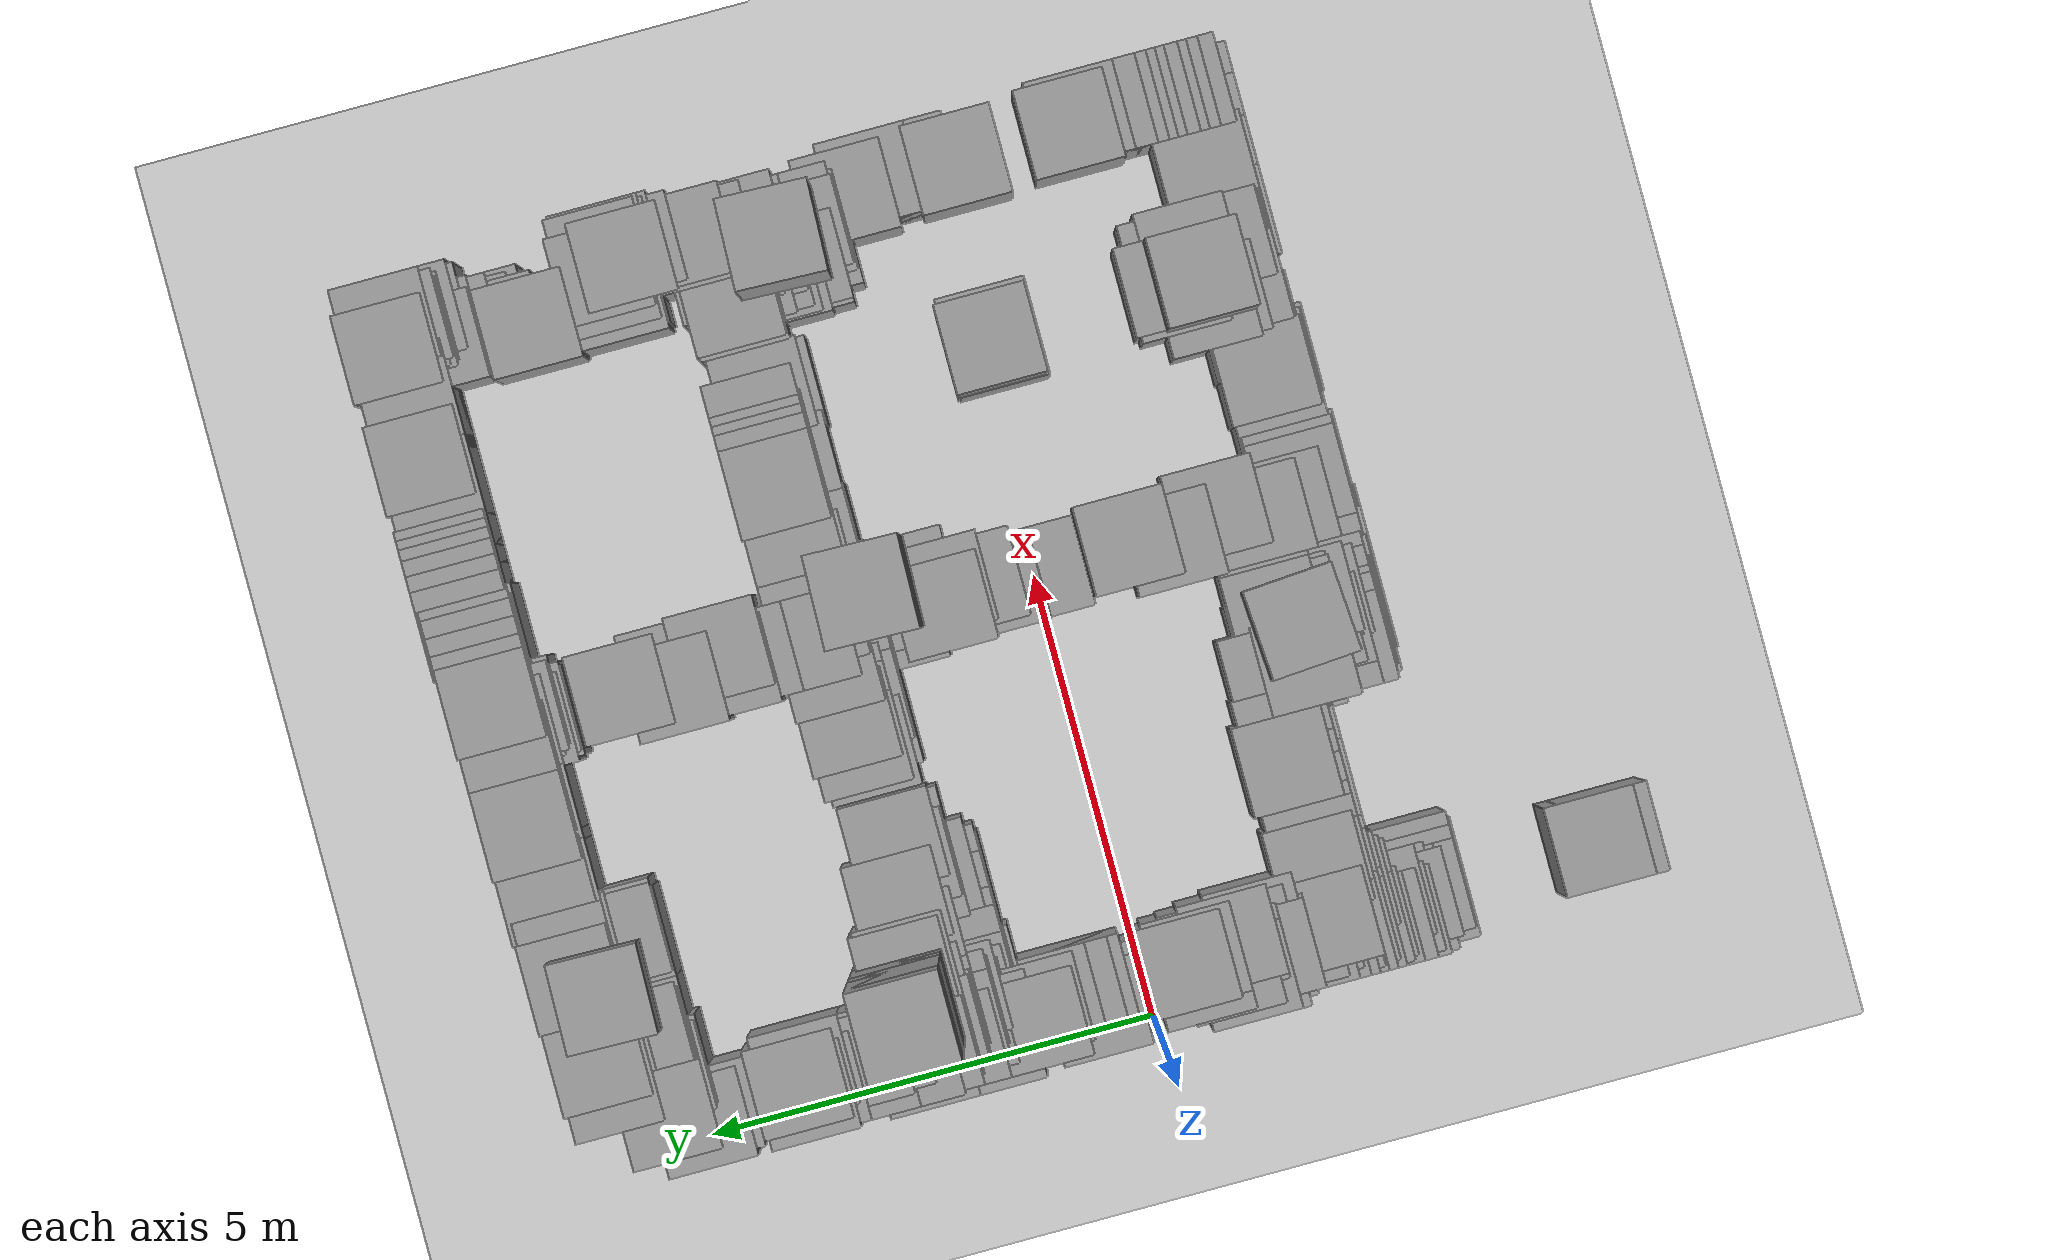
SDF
<sdf version='1.7'>
  <world name='default'>
    <light name='sun' type='directional'>
      <cast_shadows>1</cast_shadows>
      <pose>0 0 10 0 -0 0</pose>
      <diffuse>0.8 0.8 0.8 1</diffuse>
      <specular>0.2 0.2 0.2 1</specular>
      <attenuation>
        <range>1000</range>
        <constant>0.9</constant>
        <linear>0.01</linear>
        <quadratic>0.001</quadratic>
      </attenuation>
      <direction>-0.5 0.1 -0.9</direction>
      <spot>
        <inner_angle>0</inner_angle>
        <outer_angle>0</outer_angle>
        <falloff>0</falloff>
      </spot>
    </light>
    <model name='ground_plane'>
      <static>1</static>
      <link name='link'>
        <collision name='collision'>
          <geometry>
            <plane>
              <normal>0 0 1</normal>
              <size>100 100</size>
            </plane>
          </geometry>
          <surface>
            <contact>
              <collide_bitmask>65535</collide_bitmask>
              <ode/>
            </contact>
            <friction>
              <ode>
                <mu>100</mu>
                <mu2>50</mu2>
              </ode>
              <torsional>
                <ode/>
              </torsional>
            </friction>
            <bounce/>
          </surface>
          <max_contacts>10</max_contacts>
        </collision>
        <visual name='visual'>
          <cast_shadows>0</cast_shadows>
          <geometry>
            <plane>
              <normal>0 0 1</normal>
              <size>100 100</size>
            </plane>
          </geometry>
          <material>
            <script>
              <uri>file://media/materials/scripts/gazebo.material</uri>
              <name>Gazebo/Grey</name>
            </script>
          </material>
        </visual>
        <self_collide>0</self_collide>
        <enable_wind>0</enable_wind>
        <kinematic>0</kinematic>
      </link>
    </model>
    <gravity>0 0 -9.8</gravity>
    <magnetic_field>6e-06 2.3e-05 -4.2e-05</magnetic_field>
    <atmosphere type='adiabatic'/>
    <physics type='ode'>
      <max_step_size>0.001</max_step_size>
      <real_time_factor>1</real_time_factor>
      <real_time_update_rate>1000</real_time_update_rate>
    </physics>
    <scene>
      <ambient>0.4 0.4 0.4 1</ambient>
      <background>0.7 0.7 0.7 1</background>
      <shadows>1</shadows>
    </scene>
    <wind/>
    <spherical_coordinates>
      <surface_model>EARTH_WGS84</surface_model>
      <latitude_deg>0</latitude_deg>
      <longitude_deg>0</longitude_deg>
      <elevation>0</elevation>
      <heading_deg>0</heading_deg>
    </spherical_coordinates>
    <gui fullscreen='0'>
      <camera name='user_camera'>
        <pose>-2.70813 5.70495 19.0216 2e-06 1.5418 -1.5749</pose>
        <view_controller>orbit</view_controller>
        <projection_type>perspective</projection_type>
      </camera>
    </gui>

    <include>
      <uri>model://unit_box</uri>
      <name>map_box_0</name>
      <pose>9.18219 6.09754 0.15000 0.00000 0.00000 0.00000</pose>
      <scale>0.50000 0.10000 0.30000</scale>
    </include>
    <include>
      <uri>model://unit_box</uri>
      <name>map_box_1</name>
      <pose>5.20719 6.02254 0.15000 0.00000 0.00000 0.00000</pose>
      <scale>0.05000 0.15000 0.30000</scale>
    </include>
    <include>
      <uri>model://unit_box</uri>
      <name>map_box_2</name>
      <pose>5.35719 6.02254 0.15000 0.00000 0.00000 0.00000</pose>
      <scale>0.05000 0.15000 0.30000</scale>
    </include>
    <include>
      <uri>model://unit_box</uri>
      <name>map_box_3</name>
      <pose>5.55719 6.02254 0.15000 0.00000 0.00000 0.00000</pose>
      <scale>0.25000 0.15000 0.30000</scale>
    </include>
    <include>
      <uri>model://unit_box</uri>
      <name>map_box_4</name>
      <pose>5.75719 6.02254 0.15000 0.00000 0.00000 0.00000</pose>
      <scale>0.05000 0.15000 0.30000</scale>
    </include>
    <include>
      <uri>model://unit_box</uri>
      <name>map_box_5</name>
      <pose>5.85719 6.02254 0.15000 0.00000 0.00000 0.00000</pose>
      <scale>0.05000 0.15000 0.30000</scale>
    </include>
    <include>
      <uri>model://unit_box</uri>
      <name>map_box_6</name>
      <pose>6.08219 6.04754 0.15000 0.00000 0.00000 0.00000</pose>
      <scale>0.10000 0.10000 0.30000</scale>
    </include>
    <include>
      <uri>model://unit_box</uri>
      <name>map_box_7</name>
      <pose>6.25719 6.04754 0.15000 0.00000 0.00000 0.00000</pose>
      <scale>0.15000 0.10000 0.30000</scale>
    </include>
    <include>
      <uri>model://unit_box</uri>
      <name>map_box_8</name>
      <pose>6.43219 6.04754 0.15000 0.00000 0.00000 0.00000</pose>
      <scale>0.10000 0.10000 0.30000</scale>
    </include>
    <include>
      <uri>model://unit_box</uri>
      <name>map_box_9</name>
      <pose>6.55719 6.04754 0.15000 0.00000 0.00000 0.00000</pose>
      <scale>0.05000 0.10000 0.30000</scale>
    </include>
    <include>
      <uri>model://unit_box</uri>
      <name>map_box_10</name>
      <pose>6.65719 6.04754 0.15000 0.00000 0.00000 0.00000</pose>
      <scale>0.05000 0.10000 0.30000</scale>
    </include>
    <include>
      <uri>model://unit_box</uri>
      <name>map_box_11</name>
      <pose>6.75719 6.04754 0.15000 0.00000 0.00000 0.00000</pose>
      <scale>0.05000 0.10000 0.30000</scale>
    </include>
    <include>
      <uri>model://unit_box</uri>
      <name>map_box_12</name>
      <pose>7.93219 6.07254 0.15000 0.00000 0.00000 0.00000</pose>
      <scale>2.00000 0.05000 0.30000</scale>
    </include>
    <include>
      <uri>model://unit_box</uri>
      <name>map_box_13</name>
      <pose>9.45719 6.04754 0.15000 0.00000 0.00000 0.00000</pose>
      <scale>0.05000 0.10000 0.30000</scale>
    </include>
    <include>
      <uri>model://unit_box</uri>
      <name>map_box_14</name>
      <pose>3.83219 5.99754 0.15000 0.00000 0.00000 0.00000</pose>
      <scale>0.10000 0.10000 0.30000</scale>
    </include>
    <include>
      <uri>model://unit_box</uri>
      <name>map_box_15</name>
      <pose>4.40719 5.99754 0.15000 0.00000 0.00000 0.00000</pose>
      <scale>0.05000 0.10000 0.30000</scale>
    </include>
    <include>
      <uri>model://unit_box</uri>
      <name>map_box_16</name>
      <pose>4.55719 5.99754 0.15000 0.00000 0.00000 0.00000</pose>
      <scale>0.05000 0.10000 0.30000</scale>
    </include>
    <include>
      <uri>model://unit_box</uri>
      <name>map_box_17</name>
      <pose>4.73219 5.99754 0.15000 0.00000 0.00000 0.00000</pose>
      <scale>0.20000 0.10000 0.30000</scale>
    </include>
    <include>
      <uri>model://unit_box</uri>
      <name>map_box_18</name>
      <pose>5.10719 5.99754 0.15000 0.00000 0.00000 0.00000</pose>
      <scale>0.15000 0.10000 0.30000</scale>
    </include>
    <include>
      <uri>model://unit_box</uri>
      <name>map_box_19</name>
      <pose>5.28219 5.99754 0.15000 0.00000 0.00000 0.00000</pose>
      <scale>0.10000 0.10000 0.30000</scale>
    </include>
    <include>
      <uri>model://unit_box</uri>
      <name>map_box_20</name>
      <pose>5.40719 5.99754 0.15000 0.00000 0.00000 0.00000</pose>
      <scale>0.05000 0.10000 0.30000</scale>
    </include>
    <include>
      <uri>model://unit_box</uri>
      <name>map_box_21</name>
      <pose>5.70719 5.99754 0.15000 0.00000 0.00000 0.00000</pose>
      <scale>0.05000 0.10000 0.30000</scale>
    </include>
    <include>
      <uri>model://unit_box</uri>
      <name>map_box_22</name>
      <pose>5.80719 5.99754 0.15000 0.00000 0.00000 0.00000</pose>
      <scale>0.05000 0.10000 0.30000</scale>
    </include>
    <include>
      <uri>model://unit_box</uri>
      <name>map_box_23</name>
      <pose>5.95719 6.02254 0.15000 0.00000 0.00000 0.00000</pose>
      <scale>0.15000 0.05000 0.30000</scale>
    </include>
    <include>
      <uri>model://unit_box</uri>
      <name>map_box_24</name>
      <pose>6.15719 6.02254 0.15000 0.00000 0.00000 0.00000</pose>
      <scale>0.05000 0.05000 0.30000</scale>
    </include>
    <include>
      <uri>model://unit_box</uri>
      <name>map_box_25</name>
      <pose>6.35719 6.02254 0.15000 0.00000 0.00000 0.00000</pose>
      <scale>0.05000 0.05000 0.30000</scale>
    </include>
    <include>
      <uri>model://unit_box</uri>
      <name>map_box_26</name>
      <pose>6.50719 6.02254 0.15000 0.00000 0.00000 0.00000</pose>
      <scale>0.05000 0.05000 0.30000</scale>
    </include>
    <include>
      <uri>model://unit_box</uri>
      <name>map_box_27</name>
      <pose>6.60719 6.02254 0.15000 0.00000 0.00000 0.00000</pose>
      <scale>0.05000 0.05000 0.30000</scale>
    </include>
    <include>
      <uri>model://unit_box</uri>
      <name>map_box_28</name>
      <pose>6.70719 6.02254 0.15000 0.00000 0.00000 0.00000</pose>
      <scale>0.05000 0.05000 0.30000</scale>
    </include>
    <include>
      <uri>model://unit_box</uri>
      <name>map_box_29</name>
      <pose>7.58219 6.02254 0.15000 0.00000 0.00000 0.00000</pose>
      <scale>1.60000 0.05000 0.30000</scale>
    </include>
    <include>
      <uri>model://unit_box</uri>
      <name>map_box_30</name>
      <pose>8.45719 6.02254 0.15000 0.00000 0.00000 0.00000</pose>
      <scale>0.05000 0.05000 0.30000</scale>
    </include>
    <include>
      <uri>model://unit_box</uri>
      <name>map_box_31</name>
      <pose>8.65719 6.02254 0.15000 0.00000 0.00000 0.00000</pose>
      <scale>0.25000 0.05000 0.30000</scale>
    </include>
    <include>
      <uri>model://unit_box</uri>
      <name>map_box_32</name>
      <pose>9.40719 5.92254 0.15000 0.00000 0.00000 0.00000</pose>
      <scale>0.05000 0.25000 0.30000</scale>
    </include>
    <include>
      <uri>model://unit_box</uri>
      <name>map_box_33</name>
      <pose>2.10719 5.94754 0.15000 0.00000 0.00000 0.00000</pose>
      <scale>0.25000 0.10000 0.30000</scale>
    </include>
    <include>
      <uri>model://unit_box</uri>
      <name>map_box_34</name>
      <pose>2.35719 5.92254 0.15000 0.00000 0.00000 0.00000</pose>
      <scale>0.05000 0.15000 0.30000</scale>
    </include>
    <include>
      <uri>model://unit_box</uri>
      <name>map_box_35</name>
      <pose>3.10719 5.97254 0.15000 0.00000 0.00000 0.00000</pose>
      <scale>1.35000 0.05000 0.30000</scale>
    </include>
    <include>
      <uri>model://unit_box</uri>
      <name>map_box_36</name>
      <pose>4.13219 5.97254 0.15000 0.00000 0.00000 0.00000</pose>
      <scale>0.50000 0.05000 0.30000</scale>
    </include>
    <include>
      <uri>model://unit_box</uri>
      <name>map_box_37</name>
      <pose>4.48219 5.97254 0.15000 0.00000 0.00000 0.00000</pose>
      <scale>0.10000 0.05000 0.30000</scale>
    </include>
    <include>
      <uri>model://unit_box</uri>
      <name>map_box_38</name>
      <pose>4.60719 5.97254 0.15000 0.00000 0.00000 0.00000</pose>
      <scale>0.05000 0.05000 0.30000</scale>
    </include>
    <include>
      <uri>model://unit_box</uri>
      <name>map_box_39</name>
      <pose>4.88219 5.92254 0.15000 0.00000 0.00000 0.00000</pose>
      <scale>0.10000 0.15000 0.30000</scale>
    </include>
    <include>
      <uri>model://unit_box</uri>
      <name>map_box_40</name>
      <pose>5.00719 5.82254 0.15000 0.00000 0.00000 0.00000</pose>
      <scale>0.05000 0.35000 0.30000</scale>
    </include>
    <include>
      <uri>model://unit_box</uri>
      <name>map_box_41</name>
      <pose>5.90719 5.97254 0.15000 0.00000 0.00000 0.00000</pose>
      <scale>0.05000 0.05000 0.30000</scale>
    </include>
    <include>
      <uri>model://unit_box</uri>
      <name>map_box_42</name>
      <pose>9.33219 5.97254 0.15000 0.00000 0.00000 0.00000</pose>
      <scale>0.10000 0.05000 0.30000</scale>
    </include>
    <include>
      <uri>model://unit_box</uri>
      <name>map_box_43</name>
      <pose>1.18219 5.92254 0.15000 0.00000 0.00000 0.00000</pose>
      <scale>1.60000 0.05000 0.30000</scale>
    </include>
    <include>
      <uri>model://unit_box</uri>
      <name>map_box_44</name>
      <pose>2.28219 5.92254 0.15000 0.00000 0.00000 0.00000</pose>
      <scale>0.10000 0.05000 0.30000</scale>
    </include>
    <include>
      <uri>model://unit_box</uri>
      <name>map_box_45</name>
      <pose>3.05719 5.92254 0.15000 0.00000 0.00000 0.00000</pose>
      <scale>1.35000 0.05000 0.30000</scale>
    </include>
    <include>
      <uri>model://unit_box</uri>
      <name>map_box_46</name>
      <pose>4.03219 5.92254 0.15000 0.00000 0.00000 0.00000</pose>
      <scale>0.10000 0.05000 0.30000</scale>
    </include>
    <include>
      <uri>model://unit_box</uri>
      <name>map_box_47</name>
      <pose>4.15719 5.92254 0.15000 0.00000 0.00000 0.00000</pose>
      <scale>0.05000 0.05000 0.30000</scale>
    </include>
    <include>
      <uri>model://unit_box</uri>
      <name>map_box_48</name>
      <pose>5.05719 5.79754 0.15000 0.00000 0.00000 0.00000</pose>
      <scale>0.05000 0.30000 0.30000</scale>
    </include>
    <include>
      <uri>model://unit_box</uri>
      <name>map_box_49</name>
      <pose>9.30719 5.89754 0.15000 0.00000 0.00000 0.00000</pose>
      <scale>0.05000 0.10000 0.30000</scale>
    </include>
    <include>
      <uri>model://unit_box</uri>
      <name>map_box_50</name>
      <pose>0.88219 5.87254 0.15000 0.00000 0.00000 0.00000</pose>
      <scale>1.00000 0.05000 0.30000</scale>
    </include>
    <include>
      <uri>model://unit_box</uri>
      <name>map_box_51</name>
      <pose>1.45719 5.87254 0.15000 0.00000 0.00000 0.00000</pose>
      <scale>0.05000 0.05000 0.30000</scale>
    </include>
    <include>
      <uri>model://unit_box</uri>
      <name>map_box_52</name>
      <pose>2.43219 5.87254 0.15000 0.00000 0.00000 0.00000</pose>
      <scale>0.10000 0.05000 0.30000</scale>
    </include>
    <include>
      <uri>model://unit_box</uri>
      <name>map_box_53</name>
      <pose>4.95719 5.87254 0.15000 0.00000 0.00000 0.00000</pose>
      <scale>0.05000 0.05000 0.30000</scale>
    </include>
    <include>
      <uri>model://unit_box</uri>
      <name>map_box_54</name>
      <pose>9.35719 5.87254 0.15000 0.00000 0.00000 0.00000</pose>
      <scale>0.05000 0.05000 0.30000</scale>
    </include>
    <include>
      <uri>model://unit_box</uri>
      <name>map_box_55</name>
      <pose>0.43219 5.34754 0.15000 0.00000 0.00000 0.00000</pose>
      <scale>0.10000 1.00000 0.30000</scale>
    </include>
    <include>
      <uri>model://unit_box</uri>
      <name>map_box_56</name>
      <pose>1.35719 5.82254 0.15000 0.00000 0.00000 0.00000</pose>
      <scale>0.05000 0.05000 0.30000</scale>
    </include>
    <include>
      <uri>model://unit_box</uri>
      <name>map_box_57</name>
      <pose>4.85719 5.74754 0.15000 0.00000 0.00000 0.00000</pose>
      <scale>0.05000 0.20000 0.30000</scale>
    </include>
    <include>
      <uri>model://unit_box</uri>
      <name>map_box_58</name>
      <pose>9.45719 5.74754 0.15000 0.00000 0.00000 0.00000</pose>
      <scale>0.05000 0.20000 0.30000</scale>
    </include>
    <include>
      <uri>model://unit_box</uri>
      <name>map_box_59</name>
      <pose>4.95719 5.69754 0.15000 0.00000 0.00000 0.00000</pose>
      <scale>0.05000 0.20000 0.30000</scale>
    </include>
    <include>
      <uri>model://unit_box</uri>
      <name>map_box_60</name>
      <pose>4.90719 5.67254 0.15000 0.00000 0.00000 0.00000</pose>
      <scale>0.05000 0.05000 0.30000</scale>
    </include>
    <include>
      <uri>model://unit_box</uri>
      <name>map_box_61</name>
      <pose>9.10719 5.59754 0.15000 0.00000 0.00000 0.00000</pose>
      <scale>0.05000 0.20000 0.30000</scale>
    </include>
    <include>
      <uri>model://unit_box</uri>
      <name>map_box_62</name>
      <pose>9.40719 5.67254 0.15000 0.00000 0.00000 0.00000</pose>
      <scale>0.05000 0.05000 0.30000</scale>
    </include>
    <include>
      <uri>model://unit_box</uri>
      <name>map_box_63</name>
      <pose>9.05719 4.57254 0.15000 0.00000 0.00000 0.00000</pose>
      <scale>0.05000 2.05000 0.30000</scale>
    </include>
    <include>
      <uri>model://unit_box</uri>
      <name>map_box_64</name>
      <pose>9.23219 5.57254 0.15000 0.00000 0.00000 0.00000</pose>
      <scale>0.10000 0.05000 0.30000</scale>
    </include>
    <include>
      <uri>model://unit_box</uri>
      <name>map_box_65</name>
      <pose>9.20719 5.37254 0.15000 0.00000 0.00000 0.00000</pose>
      <scale>0.05000 0.35000 0.30000</scale>
    </include>
    <include>
      <uri>model://unit_box</uri>
      <name>map_box_66</name>
      <pose>1.30719 5.39754 0.15000 0.00000 0.00000 0.00000</pose>
      <scale>0.05000 0.10000 0.30000</scale>
    </include>
    <include>
      <uri>model://unit_box</uri>
      <name>map_box_67</name>
      <pose>2.40719 5.37254 0.15000 0.00000 0.00000 0.00000</pose>
      <scale>0.05000 0.15000 0.30000</scale>
    </include>
    <include>
      <uri>model://unit_box</uri>
      <name>map_box_68</name>
      <pose>9.10719 4.89754 0.15000 0.00000 0.00000 0.00000</pose>
      <scale>0.05000 1.10000 0.30000</scale>
    </include>
    <include>
      <uri>model://unit_box</uri>
      <name>map_box_69</name>
      <pose>1.25719 5.37254 0.15000 0.00000 0.00000 0.00000</pose>
      <scale>0.05000 0.05000 0.30000</scale>
    </include>
    <include>
      <uri>model://unit_box</uri>
      <name>map_box_70</name>
      <pose>1.35719 5.34754 0.15000 0.00000 0.00000 0.00000</pose>
      <scale>0.05000 0.10000 0.30000</scale>
    </include>
    <include>
      <uri>model://unit_box</uri>
      <name>map_box_71</name>
      <pose>2.35719 5.34754 0.15000 0.00000 0.00000 0.00000</pose>
      <scale>0.05000 0.10000 0.30000</scale>
    </include>
    <include>
      <uri>model://unit_box</uri>
      <name>map_box_72</name>
      <pose>2.45719 5.37254 0.15000 0.00000 0.00000 0.00000</pose>
      <scale>0.05000 0.05000 0.30000</scale>
    </include>
    <include>
      <uri>model://unit_box</uri>
      <name>map_box_73</name>
      <pose>0.85719 5.29754 0.15000 0.00000 0.00000 0.00000</pose>
      <scale>0.05000 0.10000 0.30000</scale>
    </include>
    <include>
      <uri>model://unit_box</uri>
      <name>map_box_74</name>
      <pose>0.90719 5.27254 0.15000 0.00000 0.00000 0.00000</pose>
      <scale>0.05000 0.05000 0.30000</scale>
    </include>
    <include>
      <uri>model://unit_box</uri>
      <name>map_box_75</name>
      <pose>9.15719 5.14754 0.15000 0.00000 0.00000 0.00000</pose>
      <scale>0.05000 0.10000 0.30000</scale>
    </include>
    <include>
      <uri>model://unit_box</uri>
      <name>map_box_76</name>
      <pose>0.25719 4.99754 0.15000 0.00000 0.00000 0.00000</pose>
      <scale>0.05000 0.30000 0.30000</scale>
    </include>
    <include>
      <uri>model://unit_box</uri>
      <name>map_box_77</name>
      <pose>9.20719 5.02254 0.15000 0.00000 0.00000 0.00000</pose>
      <scale>0.05000 0.25000 0.30000</scale>
    </include>
    <include>
      <uri>model://unit_box</uri>
      <name>map_box_78</name>
      <pose>0.33219 4.89754 0.15000 0.00000 0.00000 0.00000</pose>
      <scale>0.10000 0.10000 0.30000</scale>
    </include>
    <include>
      <uri>model://unit_box</uri>
      <name>map_box_79</name>
      <pose>4.98219 4.64754 0.15000 0.00000 0.00000 0.00000</pose>
      <scale>0.20000 0.10000 0.30000</scale>
    </include>
    <include>
      <uri>model://unit_box</uri>
      <name>map_box_80</name>
      <pose>4.85719 4.07254 0.15000 0.00000 0.00000 0.00000</pose>
      <scale>0.05000 1.15000 0.30000</scale>
    </include>
    <include>
      <uri>model://unit_box</uri>
      <name>map_box_81</name>
      <pose>5.10719 3.49754 0.15000 0.00000 0.00000 0.00000</pose>
      <scale>0.05000 2.30000 0.30000</scale>
    </include>
    <include>
      <uri>model://unit_box</uri>
      <name>map_box_82</name>
      <pose>4.90719 3.47254 0.15000 0.00000 0.00000 0.00000</pose>
      <scale>0.05000 2.25000 0.30000</scale>
    </include>
    <include>
      <uri>model://unit_box</uri>
      <name>map_box_83</name>
      <pose>5.05719 4.04754 0.15000 0.00000 0.00000 0.00000</pose>
      <scale>0.05000 1.10000 0.30000</scale>
    </include>
    <include>
      <uri>model://unit_box</uri>
      <name>map_box_84</name>
      <pose>0.38219 3.89754 0.15000 0.00000 0.00000 0.00000</pose>
      <scale>0.20000 0.10000 0.30000</scale>
    </include>
    <include>
      <uri>model://unit_box</uri>
      <name>map_box_85</name>
      <pose>0.25719 3.84754 0.15000 0.00000 0.00000 0.00000</pose>
      <scale>0.05000 0.10000 0.30000</scale>
    </include>
    <include>
      <uri>model://unit_box</uri>
      <name>map_box_86</name>
      <pose>0.50719 3.79754 0.15000 0.00000 0.00000 0.00000</pose>
      <scale>0.05000 0.20000 0.30000</scale>
    </include>
    <include>
      <uri>model://unit_box</uri>
      <name>map_box_87</name>
      <pose>0.30719 3.72254 0.15000 0.00000 0.00000 0.00000</pose>
      <scale>0.05000 0.25000 0.30000</scale>
    </include>
    <include>
      <uri>model://unit_box</uri>
      <name>map_box_88</name>
      <pose>0.45719 3.19754 0.15000 0.00000 0.00000 0.00000</pose>
      <scale>0.05000 1.30000 0.30000</scale>
    </include>
    <include>
      <uri>model://unit_box</uri>
      <name>map_box_89</name>
      <pose>9.48219 3.39754 0.15000 0.00000 0.00000 0.00000</pose>
      <scale>0.10000 0.80000 0.30000</scale>
    </include>
    <include>
      <uri>model://unit_box</uri>
      <name>map_box_90</name>
      <pose>9.38219 3.67254 0.15000 0.00000 0.00000 0.00000</pose>
      <scale>0.10000 0.15000 0.30000</scale>
    </include>
    <include>
      <uri>model://unit_box</uri>
      <name>map_box_91</name>
      <pose>9.23219 3.64754 0.15000 0.00000 0.00000 0.00000</pose>
      <scale>0.20000 0.10000 0.30000</scale>
    </include>
    <include>
      <uri>model://unit_box</uri>
      <name>map_box_92</name>
      <pose>0.50719 2.94754 0.15000 0.00000 0.00000 0.00000</pose>
      <scale>0.05000 1.40000 0.30000</scale>
    </include>
    <include>
      <uri>model://unit_box</uri>
      <name>map_box_93</name>
      <pose>9.10719 3.59754 0.15000 0.00000 0.00000 0.00000</pose>
      <scale>0.05000 0.10000 0.30000</scale>
    </include>
    <include>
      <uri>model://unit_box</uri>
      <name>map_box_94</name>
      <pose>9.58219 3.62254 0.15000 0.00000 0.00000 0.00000</pose>
      <scale>0.10000 0.05000 0.30000</scale>
    </include>
    <include>
      <uri>model://unit_box</uri>
      <name>map_box_95</name>
      <pose>9.15719 3.57254 0.15000 0.00000 0.00000 0.00000</pose>
      <scale>0.05000 0.05000 0.30000</scale>
    </include>
    <include>
      <uri>model://unit_box</uri>
      <name>map_box_96</name>
      <pose>9.60719 3.57254 0.15000 0.00000 0.00000 0.00000</pose>
      <scale>0.05000 0.05000 0.30000</scale>
    </include>
    <include>
      <uri>model://unit_box</uri>
      <name>map_box_97</name>
      <pose>0.30719 3.17254 0.15000 0.00000 0.00000 0.00000</pose>
      <scale>0.05000 0.75000 0.30000</scale>
    </include>
    <include>
      <uri>model://unit_box</uri>
      <name>map_box_98</name>
      <pose>9.55719 3.52254 0.15000 0.00000 0.00000 0.00000</pose>
      <scale>0.05000 0.05000 0.30000</scale>
    </include>
    <include>
      <uri>model://unit_box</uri>
      <name>map_box_99</name>
      <pose>9.60719 3.47254 0.15000 0.00000 0.00000 0.00000</pose>
      <scale>0.05000 0.05000 0.30000</scale>
    </include>
    <include>
      <uri>model://unit_box</uri>
      <name>map_box_100</name>
      <pose>9.55719 3.27254 0.15000 0.00000 0.00000 0.00000</pose>
      <scale>0.05000 0.35000 0.30000</scale>
    </include>
    <include>
      <uri>model://unit_box</uri>
      <name>map_box_101</name>
      <pose>4.95719 3.22254 0.15000 0.00000 0.00000 0.00000</pose>
      <scale>0.05000 0.05000 0.30000</scale>
    </include>
    <include>
      <uri>model://unit_box</uri>
      <name>map_box_102</name>
      <pose>9.50719 2.69754 0.15000 0.00000 0.00000 0.00000</pose>
      <scale>0.05000 0.60000 0.30000</scale>
    </include>
    <include>
      <uri>model://unit_box</uri>
      <name>map_box_103</name>
      <pose>0.30719 2.67254 0.15000 0.00000 0.00000 0.00000</pose>
      <scale>0.05000 0.15000 0.30000</scale>
    </include>
    <include>
      <uri>model://unit_box</uri>
      <name>map_box_104</name>
      <pose>4.95719 2.57254 0.15000 0.00000 0.00000 0.00000</pose>
      <scale>0.05000 0.35000 0.30000</scale>
    </include>
    <include>
      <uri>model://unit_box</uri>
      <name>map_box_105</name>
      <pose>9.45719 2.72254 0.15000 0.00000 0.00000 0.00000</pose>
      <scale>0.05000 0.05000 0.30000</scale>
    </include>
    <include>
      <uri>model://unit_box</uri>
      <name>map_box_106</name>
      <pose>0.35719 2.44754 0.15000 0.00000 0.00000 0.00000</pose>
      <scale>0.05000 0.40000 0.30000</scale>
    </include>
    <include>
      <uri>model://unit_box</uri>
      <name>map_box_107</name>
      <pose>1.25719 2.47254 0.15000 0.00000 0.00000 0.00000</pose>
      <scale>0.05000 0.35000 0.30000</scale>
    </include>
    <include>
      <uri>model://unit_box</uri>
      <name>map_box_108</name>
      <pose>1.30719 2.42254 0.15000 0.00000 0.00000 0.00000</pose>
      <scale>0.05000 0.35000 0.30000</scale>
    </include>
    <include>
      <uri>model://unit_box</uri>
      <name>map_box_109</name>
      <pose>0.25719 2.52254 0.15000 0.00000 0.00000 0.00000</pose>
      <scale>0.05000 0.05000 0.30000</scale>
    </include>
    <include>
      <uri>model://unit_box</uri>
      <name>map_box_110</name>
      <pose>8.70719 2.39754 0.15000 0.00000 0.00000 0.00000</pose>
      <scale>0.05000 0.30000 0.30000</scale>
    </include>
    <include>
      <uri>model://unit_box</uri>
      <name>map_box_111</name>
      <pose>9.45719 2.47254 0.15000 0.00000 0.00000 0.00000</pose>
      <scale>0.05000 0.15000 0.30000</scale>
    </include>
    <include>
      <uri>model://unit_box</uri>
      <name>map_box_112</name>
      <pose>0.45719 2.42254 0.15000 0.00000 0.00000 0.00000</pose>
      <scale>0.05000 0.15000 0.30000</scale>
    </include>
    <include>
      <uri>model://unit_box</uri>
      <name>map_box_113</name>
      <pose>5.15719 2.42254 0.15000 0.00000 0.00000 0.00000</pose>
      <scale>0.05000 0.15000 0.30000</scale>
    </include>
    <include>
      <uri>model://unit_box</uri>
      <name>map_box_114</name>
      <pose>6.68219 2.44754 0.15000 0.00000 0.00000 0.00000</pose>
      <scale>0.20000 0.10000 0.30000</scale>
    </include>
    <include>
      <uri>model://unit_box</uri>
      <name>map_box_115</name>
      <pose>6.85719 2.44754 0.15000 0.00000 0.00000 0.00000</pose>
      <scale>0.05000 0.10000 0.30000</scale>
    </include>
    <include>
      <uri>model://unit_box</uri>
      <name>map_box_116</name>
      <pose>6.95719 2.44754 0.15000 0.00000 0.00000 0.00000</pose>
      <scale>0.05000 0.10000 0.30000</scale>
    </include>
    <include>
      <uri>model://unit_box</uri>
      <name>map_box_117</name>
      <pose>7.05719 2.44754 0.15000 0.00000 0.00000 0.00000</pose>
      <scale>0.05000 0.10000 0.30000</scale>
    </include>
    <include>
      <uri>model://unit_box</uri>
      <name>map_box_118</name>
      <pose>7.40719 2.44754 0.15000 0.00000 0.00000 0.00000</pose>
      <scale>0.55000 0.10000 0.30000</scale>
    </include>
    <include>
      <uri>model://unit_box</uri>
      <name>map_box_119</name>
      <pose>8.65719 2.37254 0.15000 0.00000 0.00000 0.00000</pose>
      <scale>0.05000 0.25000 0.30000</scale>
    </include>
    <include>
      <uri>model://unit_box</uri>
      <name>map_box_120</name>
      <pose>9.08219 2.44754 0.15000 0.00000 0.00000 0.00000</pose>
      <scale>0.70000 0.10000 0.30000</scale>
    </include>
    <include>
      <uri>model://unit_box</uri>
      <name>map_box_121</name>
      <pose>4.63219 2.39754 0.15000 0.00000 0.00000 0.00000</pose>
      <scale>0.50000 0.10000 0.30000</scale>
    </include>
    <include>
      <uri>model://unit_box</uri>
      <name>map_box_122</name>
      <pose>5.88219 2.42254 0.15000 0.00000 0.00000 0.00000</pose>
      <scale>1.40000 0.05000 0.30000</scale>
    </include>
    <include>
      <uri>model://unit_box</uri>
      <name>map_box_123</name>
      <pose>6.80719 2.42254 0.15000 0.00000 0.00000 0.00000</pose>
      <scale>0.05000 0.05000 0.30000</scale>
    </include>
    <include>
      <uri>model://unit_box</uri>
      <name>map_box_124</name>
      <pose>6.90719 2.42254 0.15000 0.00000 0.00000 0.00000</pose>
      <scale>0.05000 0.05000 0.30000</scale>
    </include>
    <include>
      <uri>model://unit_box</uri>
      <name>map_box_125</name>
      <pose>7.00719 2.42254 0.15000 0.00000 0.00000 0.00000</pose>
      <scale>0.05000 0.05000 0.30000</scale>
    </include>
    <include>
      <uri>model://unit_box</uri>
      <name>map_box_126</name>
      <pose>7.10719 2.42254 0.15000 0.00000 0.00000 0.00000</pose>
      <scale>0.05000 0.05000 0.30000</scale>
    </include>
    <include>
      <uri>model://unit_box</uri>
      <name>map_box_127</name>
      <pose>0.55719 2.32254 0.15000 0.00000 0.00000 0.00000</pose>
      <scale>0.05000 0.15000 0.30000</scale>
    </include>
    <include>
      <uri>model://unit_box</uri>
      <name>map_box_128</name>
      <pose>0.93219 2.34754 0.15000 0.00000 0.00000 0.00000</pose>
      <scale>0.60000 0.10000 0.30000</scale>
    </include>
    <include>
      <uri>model://unit_box</uri>
      <name>map_box_129</name>
      <pose>2.00719 2.34754 0.15000 0.00000 0.00000 0.00000</pose>
      <scale>1.35000 0.10000 0.30000</scale>
    </include>
    <include>
      <uri>model://unit_box</uri>
      <name>map_box_130</name>
      <pose>4.00719 2.37254 0.15000 0.00000 0.00000 0.00000</pose>
      <scale>0.75000 0.05000 0.30000</scale>
    </include>
    <include>
      <uri>model://unit_box</uri>
      <name>map_box_131</name>
      <pose>5.75719 2.37254 0.15000 0.00000 0.00000 0.00000</pose>
      <scale>1.15000 0.05000 0.30000</scale>
    </include>
    <include>
      <uri>model://unit_box</uri>
      <name>map_box_132</name>
      <pose>7.68219 2.32254 0.15000 0.00000 0.00000 0.00000</pose>
      <scale>0.10000 0.15000 0.30000</scale>
    </include>
    <include>
      <uri>model://unit_box</uri>
      <name>map_box_133</name>
      <pose>0.60719 2.29754 0.15000 0.00000 0.00000 0.00000</pose>
      <scale>0.05000 0.10000 0.30000</scale>
    </include>
    <include>
      <uri>model://unit_box</uri>
      <name>map_box_134</name>
      <pose>3.73219 2.32254 0.15000 0.00000 0.00000 0.00000</pose>
      <scale>0.30000 0.05000 0.30000</scale>
    </include>
    <include>
      <uri>model://unit_box</uri>
      <name>map_box_135</name>
      <pose>4.05719 2.32254 0.15000 0.00000 0.00000 0.00000</pose>
      <scale>0.25000 0.05000 0.30000</scale>
    </include>
    <include>
      <uri>model://unit_box</uri>
      <name>map_box_136</name>
      <pose>4.25719 2.32254 0.15000 0.00000 0.00000 0.00000</pose>
      <scale>0.05000 0.05000 0.30000</scale>
    </include>
    <include>
      <uri>model://unit_box</uri>
      <name>map_box_137</name>
      <pose>9.13219 2.29754 0.15000 0.00000 0.00000 0.00000</pose>
      <scale>0.80000 0.10000 0.30000</scale>
    </include>
    <include>
      <uri>model://unit_box</uri>
      <name>map_box_138</name>
      <pose>0.75719 2.27254 0.15000 0.00000 0.00000 0.00000</pose>
      <scale>0.25000 0.05000 0.30000</scale>
    </include>
    <include>
      <uri>model://unit_box</uri>
      <name>map_box_139</name>
      <pose>1.53219 2.27254 0.15000 0.00000 0.00000 0.00000</pose>
      <scale>0.40000 0.05000 0.30000</scale>
    </include>
    <include>
      <uri>model://unit_box</uri>
      <name>map_box_140</name>
      <pose>2.63219 2.22254 0.15000 0.00000 0.00000 0.00000</pose>
      <scale>0.10000 0.15000 0.30000</scale>
    </include>
    <include>
      <uri>model://unit_box</uri>
      <name>map_box_141</name>
      <pose>3.65719 2.24754 0.15000 0.00000 0.00000 0.00000</pose>
      <scale>0.15000 0.10000 0.30000</scale>
    </include>
    <include>
      <uri>model://unit_box</uri>
      <name>map_box_142</name>
      <pose>5.95719 2.24754 0.15000 0.00000 0.00000 0.00000</pose>
      <scale>0.05000 0.10000 0.30000</scale>
    </include>
    <include>
      <uri>model://unit_box</uri>
      <name>map_box_143</name>
      <pose>6.83219 2.24754 0.15000 0.00000 0.00000 0.00000</pose>
      <scale>1.60000 0.10000 0.30000</scale>
    </include>
    <include>
      <uri>model://unit_box</uri>
      <name>map_box_144</name>
      <pose>4.15719 2.19754 0.15000 0.00000 0.00000 0.00000</pose>
      <scale>0.05000 0.10000 0.30000</scale>
    </include>
    <include>
      <uri>model://unit_box</uri>
      <name>map_box_145</name>
      <pose>4.38219 2.19754 0.15000 0.00000 0.00000 0.00000</pose>
      <scale>0.10000 0.10000 0.30000</scale>
    </include>
    <include>
      <uri>model://unit_box</uri>
      <name>map_box_146</name>
      <pose>4.73219 2.19754 0.15000 0.00000 0.00000 0.00000</pose>
      <scale>0.40000 0.10000 0.30000</scale>
    </include>
    <include>
      <uri>model://unit_box</uri>
      <name>map_box_147</name>
      <pose>5.50719 2.22254 0.15000 0.00000 0.00000 0.00000</pose>
      <scale>0.85000 0.05000 0.30000</scale>
    </include>
    <include>
      <uri>model://unit_box</uri>
      <name>map_box_148</name>
      <pose>6.00719 2.22254 0.15000 0.00000 0.00000 0.00000</pose>
      <scale>0.05000 0.05000 0.30000</scale>
    </include>
    <include>
      <uri>model://unit_box</uri>
      <name>map_box_149</name>
      <pose>7.65719 2.22254 0.15000 0.00000 0.00000 0.00000</pose>
      <scale>0.05000 0.05000 0.30000</scale>
    </include>
    <include>
      <uri>model://unit_box</uri>
      <name>map_box_150</name>
      <pose>8.90719 2.22254 0.15000 0.00000 0.00000 0.00000</pose>
      <scale>0.05000 0.05000 0.30000</scale>
    </include>
    <include>
      <uri>model://unit_box</uri>
      <name>map_box_151</name>
      <pose>9.20719 2.22254 0.15000 0.00000 0.00000 0.00000</pose>
      <scale>0.05000 0.05000 0.30000</scale>
    </include>
    <include>
      <uri>model://unit_box</uri>
      <name>map_box_152</name>
      <pose>9.48219 2.12254 0.15000 0.00000 0.00000 0.00000</pose>
      <scale>0.10000 0.25000 0.30000</scale>
    </include>
    <include>
      <uri>model://unit_box</uri>
      <name>map_box_153</name>
      <pose>0.35719 2.14754 0.15000 0.00000 0.00000 0.00000</pose>
      <scale>0.05000 0.10000 0.30000</scale>
    </include>
    <include>
      <uri>model://unit_box</uri>
      <name>map_box_154</name>
      <pose>2.38219 2.14754 0.15000 0.00000 0.00000 0.00000</pose>
      <scale>0.40000 0.10000 0.30000</scale>
    </include>
    <include>
      <uri>model://unit_box</uri>
      <name>map_box_155</name>
      <pose>3.88219 2.17254 0.15000 0.00000 0.00000 0.00000</pose>
      <scale>0.50000 0.05000 0.30000</scale>
    </include>
    <include>
      <uri>model://unit_box</uri>
      <name>map_box_156</name>
      <pose>4.25719 2.17254 0.15000 0.00000 0.00000 0.00000</pose>
      <scale>0.15000 0.05000 0.30000</scale>
    </include>
    <include>
      <uri>model://unit_box</uri>
      <name>map_box_157</name>
      <pose>4.48219 2.17254 0.15000 0.00000 0.00000 0.00000</pose>
      <scale>0.10000 0.05000 0.30000</scale>
    </include>
    <include>
      <uri>model://unit_box</uri>
      <name>map_box_158</name>
      <pose>4.95719 1.04754 0.15000 0.00000 0.00000 0.00000</pose>
      <scale>0.05000 2.30000 0.30000</scale>
    </include>
    <include>
      <uri>model://unit_box</uri>
      <name>map_box_159</name>
      <pose>5.10719 1.82254 0.15000 0.00000 0.00000 0.00000</pose>
      <scale>0.05000 0.75000 0.30000</scale>
    </include>
    <include>
      <uri>model://unit_box</uri>
      <name>map_box_160</name>
      <pose>5.35719 2.17254 0.15000 0.00000 0.00000 0.00000</pose>
      <scale>0.15000 0.05000 0.30000</scale>
    </include>
    <include>
      <uri>model://unit_box</uri>
      <name>map_box_161</name>
      <pose>9.40719 2.17254 0.15000 0.00000 0.00000 0.00000</pose>
      <scale>0.05000 0.05000 0.30000</scale>
    </include>
    <include>
      <uri>model://unit_box</uri>
      <name>map_box_162</name>
      <pose>0.55719 2.09754 0.15000 0.00000 0.00000 0.00000</pose>
      <scale>0.25000 0.10000 0.30000</scale>
    </include>
    <include>
      <uri>model://unit_box</uri>
      <name>map_box_163</name>
      <pose>0.78219 2.09754 0.15000 0.00000 0.00000 0.00000</pose>
      <scale>0.10000 0.10000 0.30000</scale>
    </include>
    <include>
      <uri>model://unit_box</uri>
      <name>map_box_164</name>
      <pose>2.15719 2.12254 0.15000 0.00000 0.00000 0.00000</pose>
      <scale>0.05000 0.05000 0.30000</scale>
    </include>
    <include>
      <uri>model://unit_box</uri>
      <name>map_box_165</name>
      <pose>2.60719 2.12254 0.15000 0.00000 0.00000 0.00000</pose>
      <scale>0.05000 0.05000 0.30000</scale>
    </include>
    <include>
      <uri>model://unit_box</uri>
      <name>map_box_166</name>
      <pose>4.90719 1.59754 0.15000 0.00000 0.00000 0.00000</pose>
      <scale>0.05000 1.10000 0.30000</scale>
    </include>
    <include>
      <uri>model://unit_box</uri>
      <name>map_box_167</name>
      <pose>5.25719 2.12254 0.15000 0.00000 0.00000 0.00000</pose>
      <scale>0.25000 0.05000 0.30000</scale>
    </include>
    <include>
      <uri>model://unit_box</uri>
      <name>map_box_168</name>
      <pose>0.70719 2.07254 0.15000 0.00000 0.00000 0.00000</pose>
      <scale>0.05000 0.05000 0.30000</scale>
    </include>
    <include>
      <uri>model://unit_box</uri>
      <name>map_box_169</name>
      <pose>0.85719 1.99754 0.15000 0.00000 0.00000 0.00000</pose>
      <scale>0.05000 0.20000 0.30000</scale>
    </include>
    <include>
      <uri>model://unit_box</uri>
      <name>map_box_170</name>
      <pose>2.20719 1.94754 0.15000 0.00000 0.00000 0.00000</pose>
      <scale>0.05000 0.30000 0.30000</scale>
    </include>
    <include>
      <uri>model://unit_box</uri>
      <name>map_box_171</name>
      <pose>5.15719 0.99754 0.15000 0.00000 0.00000 0.00000</pose>
      <scale>0.05000 2.20000 0.30000</scale>
    </include>
    <include>
      <uri>model://unit_box</uri>
      <name>map_box_172</name>
      <pose>9.10719 2.04754 0.15000 0.00000 0.00000 0.00000</pose>
      <scale>0.05000 0.10000 0.30000</scale>
    </include>
    <include>
      <uri>model://unit_box</uri>
      <name>map_box_173</name>
      <pose>9.40719 2.04754 0.15000 0.00000 0.00000 0.00000</pose>
      <scale>0.05000 0.10000 0.30000</scale>
    </include>
    <include>
      <uri>model://unit_box</uri>
      <name>map_box_174</name>
      <pose>0.48219 2.02254 0.15000 0.00000 0.00000 0.00000</pose>
      <scale>0.10000 0.05000 0.30000</scale>
    </include>
    <include>
      <uri>model://unit_box</uri>
      <name>map_box_175</name>
      <pose>8.93219 2.02254 0.15000 0.00000 0.00000 0.00000</pose>
      <scale>0.30000 0.05000 0.30000</scale>
    </include>
    <include>
      <uri>model://unit_box</uri>
      <name>map_box_176</name>
      <pose>9.25719 2.02254 0.15000 0.00000 0.00000 0.00000</pose>
      <scale>0.25000 0.05000 0.30000</scale>
    </include>
    <include>
      <uri>model://unit_box</uri>
      <name>map_box_177</name>
      <pose>0.35719 1.22254 0.15000 0.00000 0.00000 0.00000</pose>
      <scale>0.05000 1.55000 0.30000</scale>
    </include>
    <include>
      <uri>model://unit_box</uri>
      <name>map_box_178</name>
      <pose>0.45719 1.72254 0.15000 0.00000 0.00000 0.00000</pose>
      <scale>0.05000 0.55000 0.30000</scale>
    </include>
    <include>
      <uri>model://unit_box</uri>
      <name>map_box_179</name>
      <pose>0.65719 1.97254 0.15000 0.00000 0.00000 0.00000</pose>
      <scale>0.05000 0.05000 0.30000</scale>
    </include>
    <include>
      <uri>model://unit_box</uri>
      <name>map_box_180</name>
      <pose>8.85719 1.94754 0.15000 0.00000 0.00000 0.00000</pose>
      <scale>0.15000 0.10000 0.30000</scale>
    </include>
    <include>
      <uri>model://unit_box</uri>
      <name>map_box_181</name>
      <pose>0.50719 1.17254 0.15000 0.00000 0.00000 0.00000</pose>
      <scale>0.05000 1.55000 0.30000</scale>
    </include>
    <include>
      <uri>model://unit_box</uri>
      <name>map_box_182</name>
      <pose>0.78219 1.89754 0.15000 0.00000 0.00000 0.00000</pose>
      <scale>0.10000 0.10000 0.30000</scale>
    </include>
    <include>
      <uri>model://unit_box</uri>
      <name>map_box_183</name>
      <pose>0.90719 1.84754 0.15000 0.00000 0.00000 0.00000</pose>
      <scale>0.05000 0.10000 0.30000</scale>
    </include>
    <include>
      <uri>model://unit_box</uri>
      <name>map_box_184</name>
      <pose>1.20719 1.84754 0.15000 0.00000 0.00000 0.00000</pose>
      <scale>0.25000 0.10000 0.30000</scale>
    </include>
    <include>
      <uri>model://unit_box</uri>
      <name>map_box_185</name>
      <pose>1.40719 1.84754 0.15000 0.00000 0.00000 0.00000</pose>
      <scale>0.05000 0.10000 0.30000</scale>
    </include>
    <include>
      <uri>model://unit_box</uri>
      <name>map_box_186</name>
      <pose>1.80719 1.84754 0.15000 0.00000 0.00000 0.00000</pose>
      <scale>0.35000 0.10000 0.30000</scale>
    </include>
    <include>
      <uri>model://unit_box</uri>
      <name>map_box_187</name>
      <pose>2.10719 1.84754 0.15000 0.00000 0.00000 0.00000</pose>
      <scale>0.15000 0.10000 0.30000</scale>
    </include>
    <include>
      <uri>model://unit_box</uri>
      <name>map_box_188</name>
      <pose>8.83219 1.84754 0.15000 0.00000 0.00000 0.00000</pose>
      <scale>0.10000 0.10000 0.30000</scale>
    </include>
    <include>
      <uri>model://unit_box</uri>
      <name>map_box_189</name>
      <pose>0.83219 1.82254 0.15000 0.00000 0.00000 0.00000</pose>
      <scale>0.10000 0.05000 0.30000</scale>
    </include>
    <include>
      <uri>model://unit_box</uri>
      <name>map_box_190</name>
      <pose>1.00719 1.82254 0.15000 0.00000 0.00000 0.00000</pose>
      <scale>0.15000 0.05000 0.30000</scale>
    </include>
    <include>
      <uri>model://unit_box</uri>
      <name>map_box_191</name>
      <pose>1.35719 1.82254 0.15000 0.00000 0.00000 0.00000</pose>
      <scale>0.05000 0.05000 0.30000</scale>
    </include>
    <include>
      <uri>model://unit_box</uri>
      <name>map_box_192</name>
      <pose>1.53219 1.82254 0.15000 0.00000 0.00000 0.00000</pose>
      <scale>0.20000 0.05000 0.30000</scale>
    </include>
    <include>
      <uri>model://unit_box</uri>
      <name>map_box_193</name>
      <pose>2.00719 1.82254 0.15000 0.00000 0.00000 0.00000</pose>
      <scale>0.05000 0.05000 0.30000</scale>
    </include>
    <include>
      <uri>model://unit_box</uri>
      <name>map_box_194</name>
      <pose>8.90719 1.59754 0.15000 0.00000 0.00000 0.00000</pose>
      <scale>0.05000 0.50000 0.30000</scale>
    </include>
    <include>
      <uri>model://unit_box</uri>
      <name>map_box_195</name>
      <pose>0.25719 1.77254 0.15000 0.00000 0.00000 0.00000</pose>
      <scale>0.05000 0.05000 0.30000</scale>
    </include>
    <include>
      <uri>model://unit_box</uri>
      <name>map_box_196</name>
      <pose>0.95719 1.77254 0.15000 0.00000 0.00000 0.00000</pose>
      <scale>0.05000 0.05000 0.30000</scale>
    </include>
    <include>
      <uri>model://unit_box</uri>
      <name>map_box_197</name>
      <pose>8.85719 1.59754 0.15000 0.00000 0.00000 0.00000</pose>
      <scale>0.05000 0.40000 0.30000</scale>
    </include>
    <include>
      <uri>model://unit_box</uri>
      <name>map_box_198</name>
      <pose>9.25719 1.49754 0.15000 0.00000 0.00000 0.00000</pose>
      <scale>0.05000 0.20000 0.30000</scale>
    </include>
    <include>
      <uri>model://unit_box</uri>
      <name>map_box_199</name>
      <pose>9.40719 1.52254 0.15000 0.00000 0.00000 0.00000</pose>
      <scale>0.15000 0.15000 0.30000</scale>
    </include>
    <include>
      <uri>model://unit_box</uri>
      <name>map_box_200</name>
      <pose>9.18219 1.47254 0.15000 0.00000 0.00000 0.00000</pose>
      <scale>0.10000 0.15000 0.30000</scale>
    </include>
    <include>
      <uri>model://unit_box</uri>
      <name>map_box_201</name>
      <pose>9.30719 1.47254 0.15000 0.00000 0.00000 0.00000</pose>
      <scale>0.05000 0.15000 0.30000</scale>
    </include>
    <include>
      <uri>model://unit_box</uri>
      <name>map_box_202</name>
      <pose>9.50719 0.89754 0.15000 0.00000 0.00000 0.00000</pose>
      <scale>0.05000 1.30000 0.30000</scale>
    </include>
    <include>
      <uri>model://unit_box</uri>
      <name>map_box_203</name>
      <pose>9.03219 1.44754 0.15000 0.00000 0.00000 0.00000</pose>
      <scale>0.20000 0.10000 0.30000</scale>
    </include>
    <include>
      <uri>model://unit_box</uri>
      <name>map_box_204</name>
      <pose>9.55719 -0.35246 0.15000 0.00000 0.00000 0.00000</pose>
      <scale>0.05000 3.70000 0.30000</scale>
    </include>
    <include>
      <uri>model://unit_box</uri>
      <name>map_box_205</name>
      <pose>5.10719 0.64754 0.15000 0.00000 0.00000 0.00000</pose>
      <scale>0.05000 1.50000 0.30000</scale>
    </include>
    <include>
      <uri>model://unit_box</uri>
      <name>map_box_206</name>
      <pose>5.30719 1.34754 0.15000 0.00000 0.00000 0.00000</pose>
      <scale>0.25000 0.10000 0.30000</scale>
    </include>
    <include>
      <uri>model://unit_box</uri>
      <name>map_box_207</name>
      <pose>0.55719 1.02254 0.15000 0.00000 0.00000 0.00000</pose>
      <scale>0.05000 0.15000 0.30000</scale>
    </include>
    <include>
      <uri>model://unit_box</uri>
      <name>map_box_208</name>
      <pose>0.55719 0.77254 0.15000 0.00000 0.00000 0.00000</pose>
      <scale>0.05000 0.05000 0.30000</scale>
    </include>
    <include>
      <uri>model://unit_box</uri>
      <name>map_box_209</name>
      <pose>5.00719 0.44754 0.15000 0.00000 0.00000 0.00000</pose>
      <scale>0.05000 0.60000 0.30000</scale>
    </include>
    <include>
      <uri>model://unit_box</uri>
      <name>map_box_210</name>
      <pose>0.55719 0.64754 0.15000 0.00000 0.00000 0.00000</pose>
      <scale>0.05000 0.10000 0.30000</scale>
    </include>
    <include>
      <uri>model://unit_box</uri>
      <name>map_box_211</name>
      <pose>9.60719 0.59754 0.15000 0.00000 0.00000 0.00000</pose>
      <scale>0.05000 0.20000 0.30000</scale>
    </include>
    <include>
      <uri>model://unit_box</uri>
      <name>map_box_212</name>
      <pose>0.30719 0.57254 0.15000 0.00000 0.00000 0.00000</pose>
      <scale>0.05000 0.05000 0.30000</scale>
    </include>
    <include>
      <uri>model://unit_box</uri>
      <name>map_box_213</name>
      <pose>0.45719 0.52254 0.15000 0.00000 0.00000 0.00000</pose>
      <scale>0.05000 0.15000 0.30000</scale>
    </include>
    <include>
      <uri>model://unit_box</uri>
      <name>map_box_214</name>
      <pose>0.40719 0.52254 0.15000 0.00000 0.00000 0.00000</pose>
      <scale>0.05000 0.05000 0.30000</scale>
    </include>
    <include>
      <uri>model://unit_box</uri>
      <name>map_box_215</name>
      <pose>9.60719 0.17254 0.15000 0.00000 0.00000 0.00000</pose>
      <scale>0.05000 0.45000 0.30000</scale>
    </include>
    <include>
      <uri>model://unit_box</uri>
      <name>map_box_216</name>
      <pose>5.03219 -0.05246 0.15000 0.00000 0.00000 0.00000</pose>
      <scale>0.10000 0.10000 0.30000</scale>
    </include>
    <include>
      <uri>model://unit_box</uri>
      <name>map_box_217</name>
      <pose>7.55719 -0.22746 0.15000 0.00000 0.00000 0.00000</pose>
      <scale>0.15000 0.15000 0.30000</scale>
    </include>
    <include>
      <uri>model://unit_box</uri>
      <name>map_box_218</name>
      <pose>7.65719 -0.22746 0.15000 0.00000 0.00000 0.00000</pose>
      <scale>0.05000 0.05000 0.30000</scale>
    </include>
    <include>
      <uri>model://unit_box</uri>
      <name>map_box_219</name>
      <pose>9.60719 -1.62746 0.15000 0.00000 0.00000 0.00000</pose>
      <scale>0.05000 2.75000 0.30000</scale>
    </include>
    <include>
      <uri>model://unit_box</uri>
      <name>map_box_220</name>
      <pose>0.53219 -0.47746 0.15000 0.00000 0.00000 0.00000</pose>
      <scale>0.20000 0.05000 0.30000</scale>
    </include>
    <include>
      <uri>model://unit_box</uri>
      <name>map_box_221</name>
      <pose>0.58219 -0.60246 0.15000 0.00000 0.00000 0.00000</pose>
      <scale>0.10000 0.20000 0.30000</scale>
    </include>
    <include>
      <uri>model://unit_box</uri>
      <name>map_box_222</name>
      <pose>0.38219 -0.60246 0.15000 0.00000 0.00000 0.00000</pose>
      <scale>0.10000 0.10000 0.30000</scale>
    </include>
    <include>
      <uri>model://unit_box</uri>
      <name>map_box_223</name>
      <pose>0.65719 -1.02746 0.15000 0.00000 0.00000 0.00000</pose>
      <scale>0.05000 0.95000 0.30000</scale>
    </include>
    <include>
      <uri>model://unit_box</uri>
      <name>map_box_224</name>
      <pose>0.35719 -0.92746 0.15000 0.00000 0.00000 0.00000</pose>
      <scale>0.05000 0.55000 0.30000</scale>
    </include>
    <include>
      <uri>model://unit_box</uri>
      <name>map_box_225</name>
      <pose>0.60719 -0.80246 0.15000 0.00000 0.00000 0.00000</pose>
      <scale>0.05000 0.20000 0.30000</scale>
    </include>
    <include>
      <uri>model://unit_box</uri>
      <name>map_box_226</name>
      <pose>0.40719 -0.77746 0.15000 0.00000 0.00000 0.00000</pose>
      <scale>0.05000 0.05000 0.30000</scale>
    </include>
    <include>
      <uri>model://unit_box</uri>
      <name>map_box_227</name>
      <pose>0.40719 -0.87746 0.15000 0.00000 0.00000 0.00000</pose>
      <scale>0.05000 0.05000 0.30000</scale>
    </include>
    <include>
      <uri>model://unit_box</uri>
      <name>map_box_228</name>
      <pose>0.60719 -1.02746 0.15000 0.00000 0.00000 0.00000</pose>
      <scale>0.05000 0.15000 0.30000</scale>
    </include>
    <include>
      <uri>model://unit_box</uri>
      <name>map_box_229</name>
      <pose>0.25719 -1.07746 0.15000 0.00000 0.00000 0.00000</pose>
      <scale>0.05000 0.05000 0.30000</scale>
    </include>
    <include>
      <uri>model://unit_box</uri>
      <name>map_box_230</name>
      <pose>0.43219 -1.07746 0.15000 0.00000 0.00000 0.00000</pose>
      <scale>0.10000 0.05000 0.30000</scale>
    </include>
    <include>
      <uri>model://unit_box</uri>
      <name>map_box_231</name>
      <pose>5.10719 -1.07746 0.15000 0.00000 0.00000 0.00000</pose>
      <scale>0.25000 0.05000 0.30000</scale>
    </include>
    <include>
      <uri>model://unit_box</uri>
      <name>map_box_232</name>
      <pose>0.40719 -1.37746 0.15000 0.00000 0.00000 0.00000</pose>
      <scale>0.05000 0.55000 0.30000</scale>
    </include>
    <include>
      <uri>model://unit_box</uri>
      <name>map_box_233</name>
      <pose>4.98219 -1.52746 0.15000 0.00000 0.00000 0.00000</pose>
      <scale>0.10000 0.85000 0.30000</scale>
    </include>
    <include>
      <uri>model://unit_box</uri>
      <name>map_box_234</name>
      <pose>5.18219 -2.07746 0.15000 0.00000 0.00000 0.00000</pose>
      <scale>0.10000 1.95000 0.30000</scale>
    </include>
    <include>
      <uri>model://unit_box</uri>
      <name>map_box_235</name>
      <pose>0.25719 -1.17746 0.15000 0.00000 0.00000 0.00000</pose>
      <scale>0.05000 0.05000 0.30000</scale>
    </include>
    <include>
      <uri>model://unit_box</uri>
      <name>map_box_236</name>
      <pose>0.60719 -1.20246 0.15000 0.00000 0.00000 0.00000</pose>
      <scale>0.05000 0.10000 0.30000</scale>
    </include>
    <include>
      <uri>model://unit_box</uri>
      <name>map_box_237</name>
      <pose>0.70719 -1.32746 0.15000 0.00000 0.00000 0.00000</pose>
      <scale>0.05000 0.25000 0.30000</scale>
    </include>
    <include>
      <uri>model://unit_box</uri>
      <name>map_box_238</name>
      <pose>0.35719 -1.27746 0.15000 0.00000 0.00000 0.00000</pose>
      <scale>0.05000 0.05000 0.30000</scale>
    </include>
    <include>
      <uri>model://unit_box</uri>
      <name>map_box_239</name>
      <pose>0.60719 -1.32746 0.15000 0.00000 0.00000 0.00000</pose>
      <scale>0.05000 0.05000 0.30000</scale>
    </include>
    <include>
      <uri>model://unit_box</uri>
      <name>map_box_240</name>
      <pose>0.45719 -1.37746 0.15000 0.00000 0.00000 0.00000</pose>
      <scale>0.05000 0.05000 0.30000</scale>
    </include>
    <include>
      <uri>model://unit_box</uri>
      <name>map_box_241</name>
      <pose>0.58219 -2.07746 0.15000 0.00000 0.00000 0.00000</pose>
      <scale>0.10000 1.35000 0.30000</scale>
    </include>
    <include>
      <uri>model://unit_box</uri>
      <name>map_box_242</name>
      <pose>0.45719 -1.65246 0.15000 0.00000 0.00000 0.00000</pose>
      <scale>0.05000 0.10000 0.30000</scale>
    </include>
    <include>
      <uri>model://unit_box</uri>
      <name>map_box_243</name>
      <pose>0.40719 -1.75246 0.15000 0.00000 0.00000 0.00000</pose>
      <scale>0.05000 0.10000 0.30000</scale>
    </include>
    <include>
      <uri>model://unit_box</uri>
      <name>map_box_244</name>
      <pose>0.50719 -1.72746 0.15000 0.00000 0.00000 0.00000</pose>
      <scale>0.05000 0.05000 0.30000</scale>
    </include>
    <include>
      <uri>model://unit_box</uri>
      <name>map_box_245</name>
      <pose>9.65719 -1.75246 0.15000 0.00000 0.00000 0.00000</pose>
      <scale>0.05000 0.10000 0.30000</scale>
    </include>
    <include>
      <uri>model://unit_box</uri>
      <name>map_box_246</name>
      <pose>0.50719 -1.82746 0.15000 0.00000 0.00000 0.00000</pose>
      <scale>0.05000 0.05000 0.30000</scale>
    </include>
    <include>
      <uri>model://unit_box</uri>
      <name>map_box_247</name>
      <pose>0.40719 -1.87746 0.15000 0.00000 0.00000 0.00000</pose>
      <scale>0.05000 0.05000 0.30000</scale>
    </include>
    <include>
      <uri>model://unit_box</uri>
      <name>map_box_248</name>
      <pose>0.40719 -1.97746 0.15000 0.00000 0.00000 0.00000</pose>
      <scale>0.05000 0.05000 0.30000</scale>
    </include>
    <include>
      <uri>model://unit_box</uri>
      <name>map_box_249</name>
      <pose>5.00719 -2.52746 0.15000 0.00000 0.00000 0.00000</pose>
      <scale>0.05000 1.15000 0.30000</scale>
    </include>
    <include>
      <uri>model://unit_box</uri>
      <name>map_box_250</name>
      <pose>9.65719 -2.00246 0.15000 0.00000 0.00000 0.00000</pose>
      <scale>0.05000 0.10000 0.30000</scale>
    </include>
    <include>
      <uri>model://unit_box</uri>
      <name>map_box_251</name>
      <pose>0.45719 -2.05246 0.15000 0.00000 0.00000 0.00000</pose>
      <scale>0.05000 0.10000 0.30000</scale>
    </include>
    <include>
      <uri>model://unit_box</uri>
      <name>map_box_252</name>
      <pose>0.40719 -2.07746 0.15000 0.00000 0.00000 0.00000</pose>
      <scale>0.05000 0.05000 0.30000</scale>
    </include>
    <include>
      <uri>model://unit_box</uri>
      <name>map_box_253</name>
      <pose>2.35719 -2.10246 0.15000 0.00000 0.00000 0.00000</pose>
      <scale>1.95000 0.10000 0.30000</scale>
    </include>
    <include>
      <uri>model://unit_box</uri>
      <name>map_box_254</name>
      <pose>1.18219 -2.12746 0.15000 0.00000 0.00000 0.00000</pose>
      <scale>0.40000 0.05000 0.30000</scale>
    </include>
    <include>
      <uri>model://unit_box</uri>
      <name>map_box_255</name>
      <pose>3.35719 -2.57746 0.15000 0.00000 0.00000 0.00000</pose>
      <scale>0.05000 0.95000 0.30000</scale>
    </include>
    <include>
      <uri>model://unit_box</uri>
      <name>map_box_256</name>
      <pose>9.65719 -2.12746 0.15000 0.00000 0.00000 0.00000</pose>
      <scale>0.05000 0.05000 0.30000</scale>
    </include>
    <include>
      <uri>model://unit_box</uri>
      <name>map_box_257</name>
      <pose>0.40719 -2.17746 0.15000 0.00000 0.00000 0.00000</pose>
      <scale>0.05000 0.05000 0.30000</scale>
    </include>
    <include>
      <uri>model://unit_box</uri>
      <name>map_box_258</name>
      <pose>1.10719 -2.17746 0.15000 0.00000 0.00000 0.00000</pose>
      <scale>0.35000 0.05000 0.30000</scale>
    </include>
    <include>
      <uri>model://unit_box</uri>
      <name>map_box_259</name>
      <pose>1.35719 -2.17746 0.15000 0.00000 0.00000 0.00000</pose>
      <scale>0.05000 0.05000 0.30000</scale>
    </include>
    <include>
      <uri>model://unit_box</uri>
      <name>map_box_260</name>
      <pose>1.50719 -2.17746 0.15000 0.00000 0.00000 0.00000</pose>
      <scale>0.05000 0.05000 0.30000</scale>
    </include>
    <include>
      <uri>model://unit_box</uri>
      <name>map_box_261</name>
      <pose>1.83219 -2.17746 0.15000 0.00000 0.00000 0.00000</pose>
      <scale>0.20000 0.05000 0.30000</scale>
    </include>
    <include>
      <uri>model://unit_box</uri>
      <name>map_box_262</name>
      <pose>2.08219 -2.17746 0.15000 0.00000 0.00000 0.00000</pose>
      <scale>0.20000 0.05000 0.30000</scale>
    </include>
    <include>
      <uri>model://unit_box</uri>
      <name>map_box_263</name>
      <pose>2.63219 -2.17746 0.15000 0.00000 0.00000 0.00000</pose>
      <scale>0.20000 0.05000 0.30000</scale>
    </include>
    <include>
      <uri>model://unit_box</uri>
      <name>map_box_264</name>
      <pose>3.30719 -2.20246 0.15000 0.00000 0.00000 0.00000</pose>
      <scale>0.05000 0.10000 0.30000</scale>
    </include>
    <include>
      <uri>model://unit_box</uri>
      <name>map_box_265</name>
      <pose>0.48219 -2.22746 0.15000 0.00000 0.00000 0.00000</pose>
      <scale>0.10000 0.05000 0.30000</scale>
    </include>
    <include>
      <uri>model://unit_box</uri>
      <name>map_box_266</name>
      <pose>0.95719 -2.22746 0.15000 0.00000 0.00000 0.00000</pose>
      <scale>0.05000 0.05000 0.30000</scale>
    </include>
    <include>
      <uri>model://unit_box</uri>
      <name>map_box_267</name>
      <pose>1.10719 -2.22746 0.15000 0.00000 0.00000 0.00000</pose>
      <scale>0.05000 0.05000 0.30000</scale>
    </include>
    <include>
      <uri>model://unit_box</uri>
      <name>map_box_268</name>
      <pose>1.95719 -2.22746 0.15000 0.00000 0.00000 0.00000</pose>
      <scale>0.15000 0.05000 0.30000</scale>
    </include>
    <include>
      <uri>model://unit_box</uri>
      <name>map_box_269</name>
      <pose>2.70719 -2.22746 0.15000 0.00000 0.00000 0.00000</pose>
      <scale>0.15000 0.05000 0.30000</scale>
    </include>
    <include>
      <uri>model://unit_box</uri>
      <name>map_box_270</name>
      <pose>7.68219 -2.22746 0.15000 0.00000 0.00000 0.00000</pose>
      <scale>0.70000 0.05000 0.30000</scale>
    </include>
    <include>
      <uri>model://unit_box</uri>
      <name>map_box_271</name>
      <pose>9.65719 -2.22746 0.15000 0.00000 0.00000 0.00000</pose>
      <scale>0.05000 0.05000 0.30000</scale>
    </include>
    <include>
      <uri>model://unit_box</uri>
      <name>map_box_272</name>
      <pose>0.40719 -2.27746 0.15000 0.00000 0.00000 0.00000</pose>
      <scale>0.05000 0.05000 0.30000</scale>
    </include>
    <include>
      <uri>model://unit_box</uri>
      <name>map_box_273</name>
      <pose>0.50719 -2.27746 0.15000 0.00000 0.00000 0.00000</pose>
      <scale>0.05000 0.05000 0.30000</scale>
    </include>
    <include>
      <uri>model://unit_box</uri>
      <name>map_box_274</name>
      <pose>0.90719 -2.27746 0.15000 0.00000 0.00000 0.00000</pose>
      <scale>0.05000 0.05000 0.30000</scale>
    </include>
    <include>
      <uri>model://unit_box</uri>
      <name>map_box_275</name>
      <pose>7.60719 -2.27746 0.15000 0.00000 0.00000 0.00000</pose>
      <scale>0.55000 0.05000 0.30000</scale>
    </include>
    <include>
      <uri>model://unit_box</uri>
      <name>map_box_276</name>
      <pose>7.98219 -2.52746 0.15000 0.00000 0.00000 0.00000</pose>
      <scale>0.10000 0.55000 0.30000</scale>
    </include>
    <include>
      <uri>model://unit_box</uri>
      <name>map_box_277</name>
      <pose>0.85719 -2.32746 0.15000 0.00000 0.00000 0.00000</pose>
      <scale>0.05000 0.05000 0.30000</scale>
    </include>
    <include>
      <uri>model://unit_box</uri>
      <name>map_box_278</name>
      <pose>3.30719 -2.40246 0.15000 0.00000 0.00000 0.00000</pose>
      <scale>0.05000 0.20000 0.30000</scale>
    </include>
    <include>
      <uri>model://unit_box</uri>
      <name>map_box_279</name>
      <pose>3.95719 -2.40246 0.15000 0.00000 0.00000 0.00000</pose>
      <scale>0.05000 0.20000 0.30000</scale>
    </include>
    <include>
      <uri>model://unit_box</uri>
      <name>map_box_280</name>
      <pose>7.35719 -2.55246 0.15000 0.00000 0.00000 0.00000</pose>
      <scale>0.05000 0.50000 0.30000</scale>
    </include>
    <include>
      <uri>model://unit_box</uri>
      <name>map_box_281</name>
      <pose>7.90719 -2.32746 0.15000 0.00000 0.00000 0.00000</pose>
      <scale>0.05000 0.05000 0.30000</scale>
    </include>
    <include>
      <uri>model://unit_box</uri>
      <name>map_box_282</name>
      <pose>9.65719 -2.32746 0.15000 0.00000 0.00000 0.00000</pose>
      <scale>0.05000 0.05000 0.30000</scale>
    </include>
    <include>
      <uri>model://unit_box</uri>
      <name>map_box_283</name>
      <pose>0.43219 -2.37746 0.15000 0.00000 0.00000 0.00000</pose>
      <scale>0.10000 0.05000 0.30000</scale>
    </include>
    <include>
      <uri>model://unit_box</uri>
      <name>map_box_284</name>
      <pose>0.80719 -2.37746 0.15000 0.00000 0.00000 0.00000</pose>
      <scale>0.05000 0.05000 0.30000</scale>
    </include>
    <include>
      <uri>model://unit_box</uri>
      <name>map_box_285</name>
      <pose>3.63219 -2.37746 0.15000 0.00000 0.00000 0.00000</pose>
      <scale>0.10000 0.05000 0.30000</scale>
    </include>
    <include>
      <uri>model://unit_box</uri>
      <name>map_box_286</name>
      <pose>4.00719 -2.40246 0.15000 0.00000 0.00000 0.00000</pose>
      <scale>0.05000 0.10000 0.30000</scale>
    </include>
    <include>
      <uri>model://unit_box</uri>
      <name>map_box_287</name>
      <pose>7.40719 -2.67746 0.15000 0.00000 0.00000 0.00000</pose>
      <scale>0.05000 0.65000 0.30000</scale>
    </include>
    <include>
      <uri>model://unit_box</uri>
      <name>map_box_288</name>
      <pose>0.48219 -2.42746 0.15000 0.00000 0.00000 0.00000</pose>
      <scale>0.10000 0.05000 0.30000</scale>
    </include>
    <include>
      <uri>model://unit_box</uri>
      <name>map_box_289</name>
      <pose>3.60719 -2.45246 0.15000 0.00000 0.00000 0.00000</pose>
      <scale>0.05000 0.10000 0.30000</scale>
    </include>
    <include>
      <uri>model://unit_box</uri>
      <name>map_box_290</name>
      <pose>0.40719 -2.47746 0.15000 0.00000 0.00000 0.00000</pose>
      <scale>0.05000 0.05000 0.30000</scale>
    </include>
    <include>
      <uri>model://unit_box</uri>
      <name>map_box_291</name>
      <pose>3.55719 -2.52746 0.15000 0.00000 0.00000 0.00000</pose>
      <scale>0.05000 0.15000 0.30000</scale>
    </include>
    <include>
      <uri>model://unit_box</uri>
      <name>map_box_292</name>
      <pose>3.90719 -2.60246 0.15000 0.00000 0.00000 0.00000</pose>
      <scale>0.05000 0.30000 0.30000</scale>
    </include>
    <include>
      <uri>model://unit_box</uri>
      <name>map_box_293</name>
      <pose>9.65719 -2.47746 0.15000 0.00000 0.00000 0.00000</pose>
      <scale>0.05000 0.05000 0.30000</scale>
    </include>
    <include>
      <uri>model://unit_box</uri>
      <name>map_box_294</name>
      <pose>3.95719 -2.57746 0.15000 0.00000 0.00000 0.00000</pose>
      <scale>0.05000 0.05000 0.30000</scale>
    </include>
    <include>
      <uri>model://unit_box</uri>
      <name>map_box_295</name>
      <pose>5.05719 -2.80246 0.15000 0.00000 0.00000 0.00000</pose>
      <scale>0.05000 0.50000 0.30000</scale>
    </include>
    <include>
      <uri>model://unit_box</uri>
      <name>map_box_296</name>
      <pose>9.65719 -2.57746 0.15000 0.00000 0.00000 0.00000</pose>
      <scale>0.05000 0.05000 0.30000</scale>
    </include>
    <include>
      <uri>model://unit_box</uri>
      <name>map_box_297</name>
      <pose>0.40719 -2.62746 0.15000 0.00000 0.00000 0.00000</pose>
      <scale>0.05000 0.05000 0.30000</scale>
    </include>
    <include>
      <uri>model://unit_box</uri>
      <name>map_box_298</name>
      <pose>0.65719 -2.67746 0.15000 0.00000 0.00000 0.00000</pose>
      <scale>0.05000 0.05000 0.30000</scale>
    </include>
    <include>
      <uri>model://unit_box</uri>
      <name>map_box_299</name>
      <pose>4.00719 -2.77746 0.15000 0.00000 0.00000 0.00000</pose>
      <scale>0.05000 0.25000 0.30000</scale>
    </include>
    <include>
      <uri>model://unit_box</uri>
      <name>map_box_300</name>
      <pose>9.65719 -2.70246 0.15000 0.00000 0.00000 0.00000</pose>
      <scale>0.05000 0.10000 0.30000</scale>
    </include>
    <include>
      <uri>model://unit_box</uri>
      <name>map_box_301</name>
      <pose>0.45719 -2.72746 0.15000 0.00000 0.00000 0.00000</pose>
      <scale>0.05000 0.05000 0.30000</scale>
    </include>
    <include>
      <uri>model://unit_box</uri>
      <name>map_box_302</name>
      <pose>3.68219 -2.72746 0.15000 0.00000 0.00000 0.00000</pose>
      <scale>0.10000 0.05000 0.30000</scale>
    </include>
    <include>
      <uri>model://unit_box</uri>
      <name>map_box_303</name>
      <pose>3.95719 -2.75246 0.15000 0.00000 0.00000 0.00000</pose>
      <scale>0.05000 0.10000 0.30000</scale>
    </include>
    <include>
      <uri>model://unit_box</uri>
      <name>map_box_304</name>
      <pose>0.40719 -2.77746 0.15000 0.00000 0.00000 0.00000</pose>
      <scale>0.05000 0.05000 0.30000</scale>
    </include>
    <include>
      <uri>model://unit_box</uri>
      <name>map_box_305</name>
      <pose>0.55719 -2.95246 0.15000 0.00000 0.00000 0.00000</pose>
      <scale>0.05000 0.40000 0.30000</scale>
    </include>
    <include>
      <uri>model://unit_box</uri>
      <name>map_box_306</name>
      <pose>0.65719 -2.77746 0.15000 0.00000 0.00000 0.00000</pose>
      <scale>0.05000 0.05000 0.30000</scale>
    </include>
    <include>
      <uri>model://unit_box</uri>
      <name>map_box_307</name>
      <pose>3.65719 -2.82746 0.15000 0.00000 0.00000 0.00000</pose>
      <scale>0.05000 0.15000 0.30000</scale>
    </include>
    <include>
      <uri>model://unit_box</uri>
      <name>map_box_308</name>
      <pose>3.40719 -2.82746 0.15000 0.00000 0.00000 0.00000</pose>
      <scale>0.05000 0.05000 0.30000</scale>
    </include>
    <include>
      <uri>model://unit_box</uri>
      <name>map_box_309</name>
      <pose>7.95719 -2.87746 0.15000 0.00000 0.00000 0.00000</pose>
      <scale>0.05000 0.15000 0.30000</scale>
    </include>
    <include>
      <uri>model://unit_box</uri>
      <name>map_box_310</name>
      <pose>9.65719 -2.87746 0.15000 0.00000 0.00000 0.00000</pose>
      <scale>0.05000 0.15000 0.30000</scale>
    </include>
    <include>
      <uri>model://unit_box</uri>
      <name>map_box_311</name>
      <pose>0.43219 -2.87746 0.15000 0.00000 0.00000 0.00000</pose>
      <scale>0.10000 0.05000 0.30000</scale>
    </include>
    <include>
      <uri>model://unit_box</uri>
      <name>map_box_312</name>
      <pose>0.60719 -2.87746 0.15000 0.00000 0.00000 0.00000</pose>
      <scale>0.05000 0.05000 0.30000</scale>
    </include>
    <include>
      <uri>model://unit_box</uri>
      <name>map_box_313</name>
      <pose>3.95719 -2.87746 0.15000 0.00000 0.00000 0.00000</pose>
      <scale>0.05000 0.05000 0.30000</scale>
    </include>
    <include>
      <uri>model://unit_box</uri>
      <name>map_box_314</name>
      <pose>7.45719 -2.92746 0.15000 0.00000 0.00000 0.00000</pose>
      <scale>0.05000 0.15000 0.30000</scale>
    </include>
    <include>
      <uri>model://unit_box</uri>
      <name>map_box_315</name>
      <pose>7.90719 -2.90246 0.15000 0.00000 0.00000 0.00000</pose>
      <scale>0.05000 0.10000 0.30000</scale>
    </include>
    <include>
      <uri>model://unit_box</uri>
      <name>map_box_316</name>
      <pose>3.40719 -3.00246 0.15000 0.00000 0.00000 0.00000</pose>
      <scale>0.05000 0.20000 0.30000</scale>
    </include>
    <include>
      <uri>model://unit_box</uri>
      <name>map_box_317</name>
      <pose>3.60719 -3.00246 0.15000 0.00000 0.00000 0.00000</pose>
      <scale>0.05000 0.20000 0.30000</scale>
    </include>
    <include>
      <uri>model://unit_box</uri>
      <name>map_box_318</name>
      <pose>6.48219 -2.97746 0.15000 0.00000 0.00000 0.00000</pose>
      <scale>0.10000 0.15000 0.30000</scale>
    </include>
    <include>
      <uri>model://unit_box</uri>
      <name>map_box_319</name>
      <pose>6.98219 -2.95246 0.15000 0.00000 0.00000 0.00000</pose>
      <scale>0.80000 0.10000 0.30000</scale>
    </include>
    <include>
      <uri>model://unit_box</uri>
      <name>map_box_320</name>
      <pose>7.85719 -2.92746 0.15000 0.00000 0.00000 0.00000</pose>
      <scale>0.05000 0.05000 0.30000</scale>
    </include>
    <include>
      <uri>model://unit_box</uri>
      <name>map_box_321</name>
      <pose>8.78219 -2.92746 0.15000 0.00000 0.00000 0.00000</pose>
      <scale>1.60000 0.05000 0.30000</scale>
    </include>
    <include>
      <uri>model://unit_box</uri>
      <name>map_box_322</name>
      <pose>3.55719 -3.02746 0.15000 0.00000 0.00000 0.00000</pose>
      <scale>0.05000 0.15000 0.30000</scale>
    </include>
    <include>
      <uri>model://unit_box</uri>
      <name>map_box_323</name>
      <pose>3.68219 -3.00246 0.15000 0.00000 0.00000 0.00000</pose>
      <scale>0.10000 0.10000 0.30000</scale>
    </include>
    <include>
      <uri>model://unit_box</uri>
      <name>map_box_324</name>
      <pose>3.90719 -3.00246 0.15000 0.00000 0.00000 0.00000</pose>
      <scale>0.15000 0.10000 0.30000</scale>
    </include>
    <include>
      <uri>model://unit_box</uri>
      <name>map_box_325</name>
      <pose>4.05719 -3.00246 0.15000 0.00000 0.00000 0.00000</pose>
      <scale>0.05000 0.10000 0.30000</scale>
    </include>
    <include>
      <uri>model://unit_box</uri>
      <name>map_box_326</name>
      <pose>5.25719 -3.02746 0.15000 0.00000 0.00000 0.00000</pose>
      <scale>0.05000 0.15000 0.30000</scale>
    </include>
    <include>
      <uri>model://unit_box</uri>
      <name>map_box_327</name>
      <pose>5.35719 -3.02746 0.15000 0.00000 0.00000 0.00000</pose>
      <scale>0.05000 0.15000 0.30000</scale>
    </include>
    <include>
      <uri>model://unit_box</uri>
      <name>map_box_328</name>
      <pose>5.93219 -3.00246 0.15000 0.00000 0.00000 0.00000</pose>
      <scale>1.00000 0.10000 0.30000</scale>
    </include>
    <include>
      <uri>model://unit_box</uri>
      <name>map_box_329</name>
      <pose>6.55719 -3.00246 0.15000 0.00000 0.00000 0.00000</pose>
      <scale>0.05000 0.10000 0.30000</scale>
    </include>
    <include>
      <uri>model://unit_box</uri>
      <name>map_box_330</name>
      <pose>8.15719 -2.97746 0.15000 0.00000 0.00000 0.00000</pose>
      <scale>0.35000 0.05000 0.30000</scale>
    </include>
    <include>
      <uri>model://unit_box</uri>
      <name>map_box_331</name>
      <pose>8.70719 -2.97746 0.15000 0.00000 0.00000 0.00000</pose>
      <scale>0.65000 0.05000 0.30000</scale>
    </include>
    <include>
      <uri>model://unit_box</uri>
      <name>map_box_332</name>
      <pose>9.18219 -2.97746 0.15000 0.00000 0.00000 0.00000</pose>
      <scale>0.20000 0.05000 0.30000</scale>
    </include>
    <include>
      <uri>model://unit_box</uri>
      <name>map_box_333</name>
      <pose>9.53219 -2.97746 0.15000 0.00000 0.00000 0.00000</pose>
      <scale>0.10000 0.05000 0.30000</scale>
    </include>
    <include>
      <uri>model://unit_box</uri>
      <name>map_box_334</name>
      <pose>3.48219 -3.05246 0.15000 0.00000 0.00000 0.00000</pose>
      <scale>0.10000 0.10000 0.30000</scale>
    </include>
    <include>
      <uri>model://unit_box</uri>
      <name>map_box_335</name>
      <pose>3.78219 -3.02746 0.15000 0.00000 0.00000 0.00000</pose>
      <scale>0.10000 0.05000 0.30000</scale>
    </include>
    <include>
      <uri>model://unit_box</uri>
      <name>map_box_336</name>
      <pose>4.00719 -3.05246 0.15000 0.00000 0.00000 0.00000</pose>
      <scale>0.05000 0.10000 0.30000</scale>
    </include>
    <include>
      <uri>model://unit_box</uri>
      <name>map_box_337</name>
      <pose>4.53219 -3.02746 0.15000 0.00000 0.00000 0.00000</pose>
      <scale>0.90000 0.05000 0.30000</scale>
    </include>
    <include>
      <uri>model://unit_box</uri>
      <name>map_box_338</name>
      <pose>5.30719 -3.05246 0.15000 0.00000 0.00000 0.00000</pose>
      <scale>0.05000 0.10000 0.30000</scale>
    </include>
    <include>
      <uri>model://unit_box</uri>
      <name>map_box_339</name>
      <pose>5.40719 -3.05246 0.15000 0.00000 0.00000 0.00000</pose>
      <scale>0.05000 0.10000 0.30000</scale>
    </include>
    <include>
      <uri>model://unit_box</uri>
      <name>map_box_340</name>
      <pose>6.60719 -3.02746 0.15000 0.00000 0.00000 0.00000</pose>
      <scale>0.05000 0.05000 0.30000</scale>
    </include>
    <include>
      <uri>model://unit_box</uri>
      <name>map_box_341</name>
      <pose>0.60719 -3.10246 0.15000 0.00000 0.00000 0.00000</pose>
      <scale>0.05000 0.10000 0.30000</scale>
    </include>
    <include>
      <uri>model://unit_box</uri>
      <name>map_box_342</name>
      <pose>0.75719 -3.10246 0.15000 0.00000 0.00000 0.00000</pose>
      <scale>0.05000 0.10000 0.30000</scale>
    </include>
    <include>
      <uri>model://unit_box</uri>
      <name>map_box_343</name>
      <pose>0.90719 -3.10246 0.15000 0.00000 0.00000 0.00000</pose>
      <scale>0.05000 0.10000 0.30000</scale>
    </include>
    <include>
      <uri>model://unit_box</uri>
      <name>map_box_344</name>
      <pose>3.73219 -3.07746 0.15000 0.00000 0.00000 0.00000</pose>
      <scale>0.10000 0.05000 0.30000</scale>
    </include>
    <include>
      <uri>model://unit_box</uri>
      <name>map_box_345</name>
      <pose>4.55719 -3.07746 0.15000 0.00000 0.00000 0.00000</pose>
      <scale>0.85000 0.05000 0.30000</scale>
    </include>
    <include>
      <uri>model://unit_box</uri>
      <name>map_box_346</name>
      <pose>0.50719 -3.12746 0.15000 0.00000 0.00000 0.00000</pose>
      <scale>0.05000 0.05000 0.30000</scale>
    </include>
    <include>
      <uri>model://unit_box</uri>
      <name>map_box_347</name>
      <pose>0.68219 -3.12746 0.15000 0.00000 0.00000 0.00000</pose>
      <scale>0.10000 0.05000 0.30000</scale>
    </include>
    <include>
      <uri>model://unit_box</uri>
      <name>map_box_348</name>
      <pose>0.83219 -3.12746 0.15000 0.00000 0.00000 0.00000</pose>
      <scale>0.10000 0.05000 0.30000</scale>
    </include>
    <include>
      <uri>model://unit_box</uri>
      <name>map_box_349</name>
      <pose>0.65719 -5.12746 0.15000 0.00000 0.00000 0.00000</pose>
      <scale>0.05000 0.05000 0.30000</scale>
    </include>
    <include>
      <uri>model://unit_box</uri>
      <name>map_box_350</name>
      <pose>0.65719 -5.27746 0.15000 0.00000 0.00000 0.00000</pose>
      <scale>0.05000 0.05000 0.30000</scale>
    </include>
    <include>
      <uri>model://unit_box</uri>
      <name>side_table</name>
      <pose>3.78750 -2.62250 0.46000 0.00000 0.00000 0.07131</pose>
      <scale>0.42107 0.60033 0.28000</scale>
    </include>
    <include>
      <uri>model://unit_box</uri>
      <name>cabinet_0</name>
      <pose>5.29500 1.77750 0.05000 0.00000 0.00000 1.54641</pose>
      <scale>0.82024 0.29000 0.10000</scale>
    </include>
    <include>
      <uri>model://unit_box</uri>
      <name>cabinet_1</name>
      <pose>5.29500 1.77750 0.40500 0.00000 0.00000 1.54641</pose>
      <scale>0.82024 0.29000 0.03000</scale>
    </include>
    <include>
      <uri>model://unit_box</uri>
      <name>cabinet_2</name>
      <pose>5.29500 1.77750 0.69500 0.00000 0.00000 1.54641</pose>
      <scale>0.82024 0.29000 0.03000</scale>
    </include>
    <include>
      <uri>model://unit_box</uri>
      <name>cabinet_3</name>
      <pose>5.29500 1.77750 1.04500 0.00000 0.00000 1.54641</pose>
      <scale>0.82024 0.29000 0.03000</scale>
    </include>
    <include>
      <uri>model://unit_box</uri>
      <name>cabinet_4</name>
      <pose>5.29500 1.77750 1.46500 0.00000 0.00000 1.54641</pose>
      <scale>0.82024 0.29000 0.03000</scale>
    </include>
    <include>
      <uri>model://unit_box</uri>
      <name>cabinet_5</name>
      <pose>5.29500 1.77750 1.68500 0.00000 0.00000 1.54641</pose>
      <scale>0.82024 0.29000 0.03000</scale>
    </include>
    <include>
      <uri>model://unit_box</uri>
      <name>cabinet_6</name>
      <pose>5.29500 1.77750 2.01500 0.00000 0.00000 1.54641</pose>
      <scale>0.82024 0.29000 0.03000</scale>
    </include>
    <include>
      <uri>model://unit_box</uri>
      <name>shelf_0</name>
      <pose>0.89250 2.52500 0.05000 0.00000 0.00000 3.14159</pose>
      <scale>0.74000 0.28018 0.10000</scale>
    </include>
    <include>
      <uri>model://unit_box</uri>
      <name>shelf_1</name>
      <pose>0.89250 2.52500 0.40500 0.00000 0.00000 3.14159</pose>
      <scale>0.74000 0.28018 0.03000</scale>
    </include>
    <include>
      <uri>model://unit_box</uri>
      <name>shelf_2</name>
      <pose>0.89250 2.52500 0.69500 0.00000 0.00000 3.14159</pose>
      <scale>0.74000 0.28018 0.03000</scale>
    </include>
    <include>
      <uri>model://unit_box</uri>
      <name>shelf_3</name>
      <pose>0.89250 2.52500 1.04500 0.00000 0.00000 3.14159</pose>
      <scale>0.74000 0.28018 0.03000</scale>
    </include>
    <include>
      <uri>model://unit_box</uri>
      <name>shelf_4</name>
      <pose>0.89250 2.52500 1.46500 0.00000 0.00000 3.14159</pose>
      <scale>0.74000 0.28018 0.03000</scale>
    </include>
    <include>
      <uri>model://unit_box</uri>
      <name>shelf_5</name>
      <pose>0.89250 2.52500 1.68500 0.00000 0.00000 3.14159</pose>
      <scale>0.74000 0.28018 0.03000</scale>
    </include>
    <include>
      <uri>model://unit_box</uri>
      <name>shelf_6</name>
      <pose>0.89250 2.52500 2.01500 0.00000 0.00000 3.14159</pose>
      <scale>0.74000 0.28018 0.03000</scale>
    </include>
    <include>
      <uri>model://unit_box</uri>
      <name>dining_table</name>
      <pose>7.57000 -0.20000 0.52500 0.00000 0.00000 1.57080</pose>
      <scale>0.78000 0.80000 0.41000</scale>
    </include>
    <include>
      <uri>model://unit_box</uri>
      <name>dishwasher</name>
      <pose>7.65750 -2.56250 0.58500 0.00000 0.00000 0.00000</pose>
      <scale>0.56000 0.70007 0.53000</scale>
    </include>
    <include>
      <uri>model://unit_box</uri>
      <name>laundry_table</name>
      <pose>1.85000 5.64000 0.52500 0.00000 0.00000 -0.01887</pose>
      <scale>1.06019 0.55000 0.41000</scale>
    </include>
    <include>
      <uri>model://unit_box</uri>
      <name>refrigerator</name>
      <pose>9.16750 1.74750 1.09000 0.00000 0.00000 1.53748</pose>
      <scale>0.60033 0.60033 1.54000</scale>
    </include>
  </world>
</sdf>

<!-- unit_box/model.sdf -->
<sdf version='1.7'>
  <model name='unit_box'>
    <link name='link'>
      <inertial>
        <mass>1</mass>
        <inertia>
          <ixx>0.166667</ixx>
          <ixy>0</ixy>
          <ixz>0</ixz>
          <iyy>0.166667</iyy>
          <iyz>0</iyz>
          <izz>0.166667</izz>
        </inertia>
        <pose>0 0 0 0 -0 0</pose>
      </inertial>
      <self_collide>0</self_collide>
      <enable_wind>0</enable_wind>
      <pose>0 0 0 0 -0 0</pose>
      <gravity>1</gravity>
      <kinematic>0</kinematic>
      <visual name='visual'>
        <geometry>
          <box>
            <size>1 1 1</size>
          </box>
        </geometry>
        <material>
          <script>
            <name>Gazebo/Grey</name>
            <uri>file://media/materials/scripts/gazebo.material</uri>
          </script>
          <shader type='pixel'>
            <normal_map>__default__</normal_map>
          </shader>
          <ambient>0.8 0.8 0.8 1</ambient>
          <diffuse>0.7 0.7 0.7 1</diffuse>
          <specular>0.01 0.01 0.01 1</specular>
          <emissive>0 0 0 1</emissive>
        </material>
        <pose>0 0 0 0 -0 0</pose>
        <transparency>0</transparency>
        <cast_shadows>1</cast_shadows>
      </visual>
      <collision name='collision'>
        <laser_retro>0</laser_retro>
        <max_contacts>10</max_contacts>
        <pose>0 0 0 0 -0 0</pose>
        <geometry>
          <box>
            <size>1 1 1</size>
          </box>
        </geometry>
        <surface>
          <friction>
            <ode>
              <mu>1</mu>
              <mu2>1</mu2>
              <fdir1>0 0 0</fdir1>
              <slip1>0</slip1>
              <slip2>0</slip2>
            </ode>
            <torsional>
              <coefficient>1</coefficient>
              <patch_radius>0</patch_radius>
              <surface_radius>0</surface_radius>
              <use_patch_radius>1</use_patch_radius>
              <ode>
                <slip>0</slip>
              </ode>
            </torsional>
          </friction>
          <bounce>
            <restitution_coefficient>0</restitution_coefficient>
            <threshold>1e+06</threshold>
          </bounce>
          <contact>
            <collide_without_contact>0</collide_without_contact>
            <collide_without_contact_bitmask>1</collide_without_contact_bitmask>
            <collide_bitmask>1</collide_bitmask>
            <ode>
              <soft_cfm>0</soft_cfm>
              <soft_erp>0.2</soft_erp>
              <kp>1e+13</kp>
              <kd>1</kd>
              <max_vel>0.01</max_vel>
              <min_depth>0</min_depth>
            </ode>
            <bullet>
              <split_impulse>1</split_impulse>
              <split_impulse_penetration_threshold>-0.01</split_impulse_penetration_threshold>
              <soft_cfm>0</soft_cfm>
              <soft_erp>0.2</soft_erp>
              <kp>1e+13</kp>
              <kd>1</kd>
            </bullet>
          </contact>
        </surface>
      </collision>
    </link>
    <static>0</static>
    <allow_auto_disable>1</allow_auto_disable>
  </model>
</sdf>
